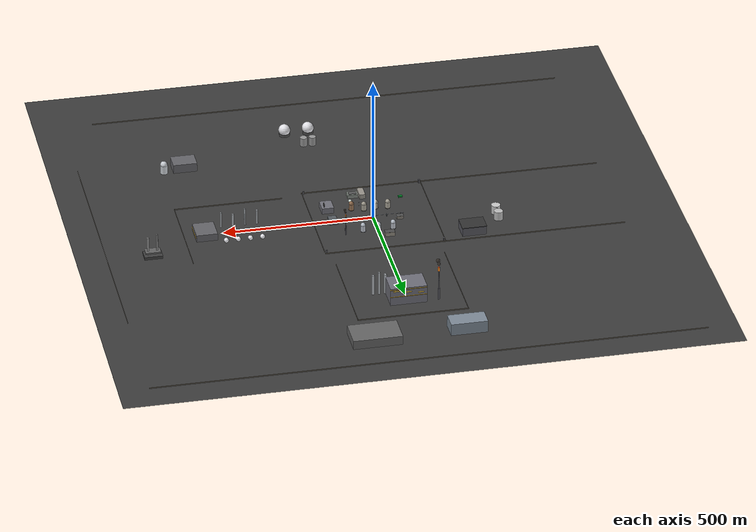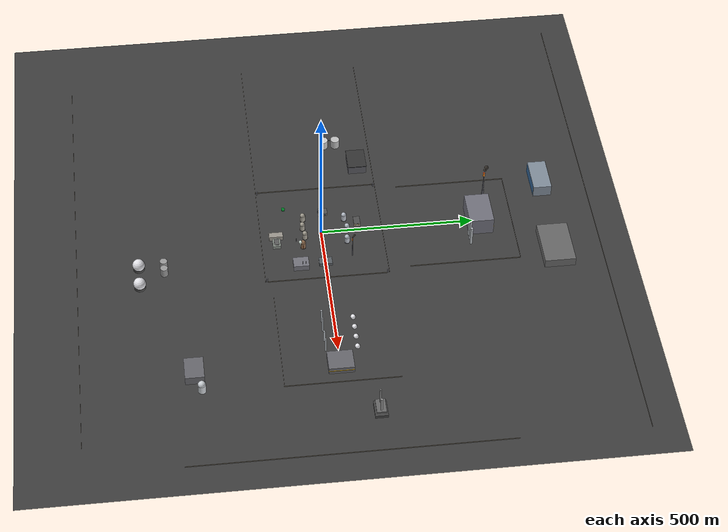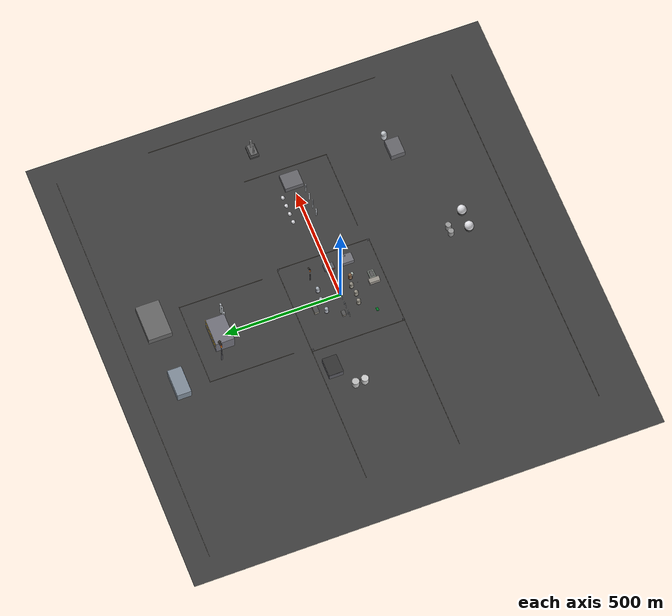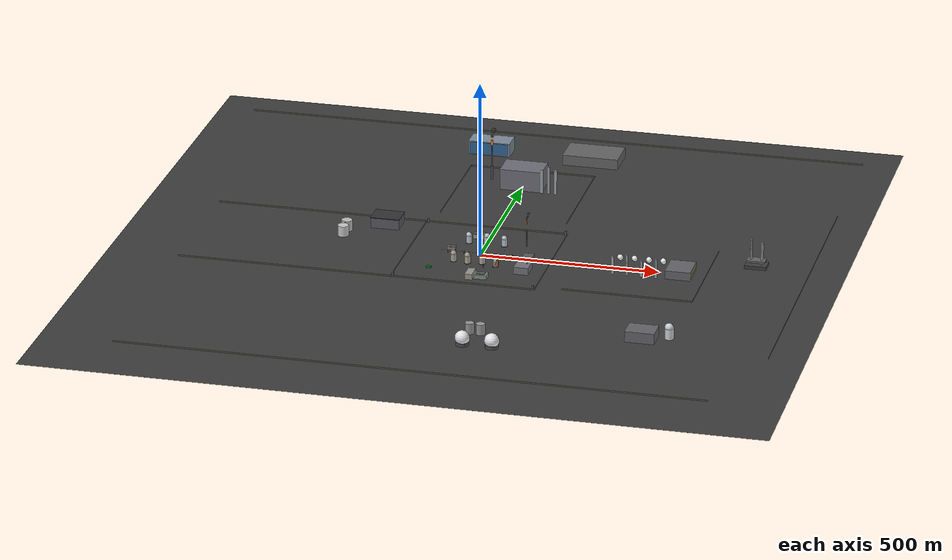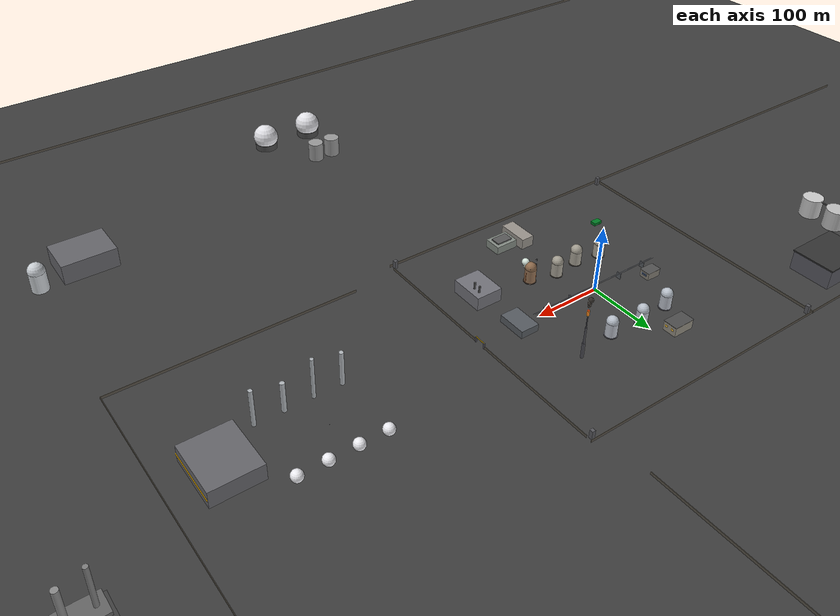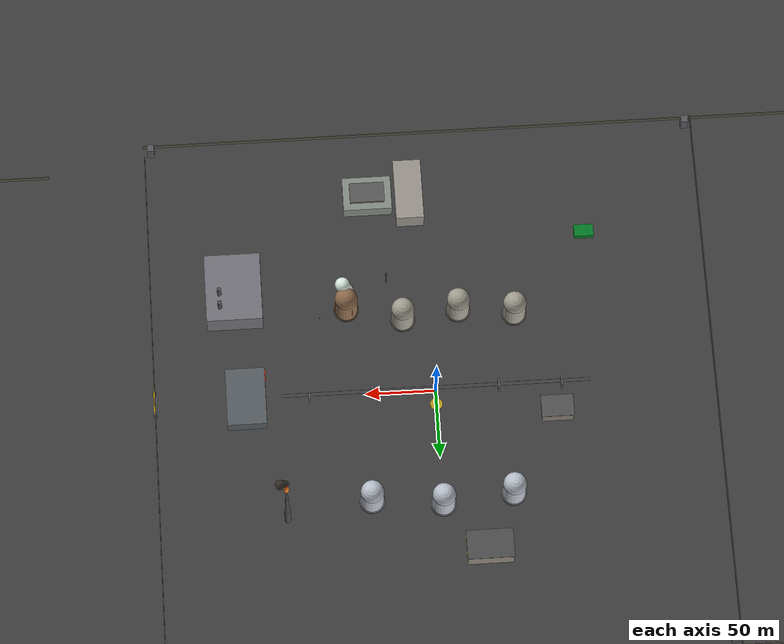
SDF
<sdf version="1.9">
 <world name="lng_terminal">
  <physics name="dart_physics" type="dart">
   <max_step_size>0.002</max_step_size>
   <real_time_factor>1.0</real_time_factor>
  </physics>
  <plugin filename="gz-sim-physics-system" name="gz::sim::systems::Physics"/>
  <plugin filename="gz-sim-scene-broadcaster-system" name="gz::sim::systems::SceneBroadcaster"/>
  <plugin filename="gz-sim-user-commands-system" name="gz::sim::systems::UserCommands"/>
  <plugin filename="gz-sim-sensors-system" name="gz::sim::systems::Sensors"/>
  <plugin filename="gz-sim-particle-emitter-system" name="gz::sim::systems::ParticleEmitter"/>
  <plugin filename="DroneAnimator" name="vesper::DroneAnimator"/>
  <scene>
   <ambient>0.26 0.24 0.22 1.0</ambient>
   <background>0.22 0.26 0.36 1.0</background>
   <shadows>true</shadows>
   <grid>false</grid>
   <origin_visual>false</origin_visual>
   <fog>
    <color>0.28 0.30 0.36 1</color>
    <type>linear</type>
    <start>200</start>
    <end>900</end>
    <density>0.0015</density>
   </fog>
  </scene>
  <light type="directional" name="moonlight">
   <pose>0 0 200 0 0 0</pose>
   <diffuse>0.32 0.34 0.42 1</diffuse>
   <specular>0.10 0.11 0.16 1</specular>
   <direction>0.3 -0.5 -0.8</direction>
   <attenuation>
    <range>3000</range>
    <constant>0.9</constant>
    <linear>0.0</linear>
    <quadratic>0.0</quadratic>
   </attenuation>
  </light>
  <light type="directional" name="dawn_hint">
   <cast_shadows>false</cast_shadows>
   <pose>0 0 100 0 0 0</pose>
   <diffuse>0.20 0.14 0.10 1</diffuse>
   <specular>0.05 0.03 0.02 1</specular>
   <direction>-0.6 -0.4 -0.5</direction>
  </light>
  <light type="point" name="fl_n">
   <cast_shadows>false</cast_shadows>
   <pose>0 150 28 0 0 0</pose>
   <diffuse>0.90 0.70 0.35 1</diffuse>
   <specular>0.18 0.12 0.04 1</specular>
   <attenuation>
    <range>220</range>
    <constant>0.3</constant>
    <linear>0.015</linear>
    <quadratic>0.0001</quadratic>
   </attenuation>
  </light>
  <light type="point" name="fl_s">
   <cast_shadows>false</cast_shadows>
   <pose>0 -150 28 0 0 0</pose>
   <diffuse>0.90 0.70 0.35 1</diffuse>
   <specular>0.18 0.12 0.04 1</specular>
   <attenuation>
    <range>220</range>
    <constant>0.3</constant>
    <linear>0.015</linear>
    <quadratic>0.0001</quadratic>
   </attenuation>
  </light>
  <light type="point" name="fl_e">
   <cast_shadows>false</cast_shadows>
   <pose>150 0 28 0 0 0</pose>
   <diffuse>0.90 0.70 0.35 1</diffuse>
   <specular>0.18 0.12 0.04 1</specular>
   <attenuation>
    <range>220</range>
    <constant>0.3</constant>
    <linear>0.015</linear>
    <quadratic>0.0001</quadratic>
   </attenuation>
  </light>
  <light type="point" name="fl_w">
   <cast_shadows>false</cast_shadows>
   <pose>-150 0 28 0 0 0</pose>
   <diffuse>0.90 0.70 0.35 1</diffuse>
   <specular>0.18 0.12 0.04 1</specular>
   <attenuation>
    <range>220</range>
    <constant>0.3</constant>
    <linear>0.015</linear>
    <quadratic>0.0001</quadratic>
   </attenuation>
  </light>
  <light type="point" name="sector2_glow">
   <cast_shadows>false</cast_shadows>
   <pose>450 0 40 0 0 0</pose>
   <diffuse>0.80 0.55 0.20 1</diffuse>
   <specular>0.1 0.08 0.02 1</specular>
   <attenuation>
    <range>400</range>
    <constant>0.3</constant>
    <linear>0.008</linear>
    <quadratic>0.00003</quadratic>
   </attenuation>
  </light>
  <light type="point" name="sector3_glow">
   <cast_shadows>false</cast_shadows>
   <pose>0 450 60 0 0 0</pose>
   <diffuse>0.78 0.52 0.18 1</diffuse>
   <specular>0.08 0.06 0.02 1</specular>
   <attenuation>
    <range>400</range>
    <constant>0.3</constant>
    <linear>0.008</linear>
    <quadratic>0.00003</quadratic>
   </attenuation>
  </light>
  <light type="point" name="emrg1">
   <cast_shadows>false</cast_shadows>
   <pose>60 -58 5 0 0 0</pose>
   <diffuse>1.0 0.05 0.03 1</diffuse>
   <specular>0.4 0.01 0.01 1</specular>
   <attenuation>
    <range>40</range>
    <constant>0.2</constant>
    <linear>0.07</linear>
    <quadratic>0.03</quadratic>
   </attenuation>
  </light>
  <light type="point" name="emrg2">
   <cast_shadows>false</cast_shadows>
   <pose>40 -65 5 0 0 0</pose>
   <diffuse>1.0 0.05 0.03 1</diffuse>
   <specular>0.3 0.01 0.01 1</specular>
   <attenuation>
    <range>35</range>
    <constant>0.2</constant>
    <linear>0.07</linear>
    <quadratic>0.03</quadratic>
   </attenuation>
  </light>
  <light type="point" name="flare_glow">
   <cast_shadows>false</cast_shadows>
   <pose>110 90 60 0 0 0</pose>
   <diffuse>1.0 0.42 0.06 1</diffuse>
   <specular>0.5 0.18 0.01 1</specular>
   <attenuation>
    <range>160</range>
    <constant>0.25</constant>
    <linear>0.02</linear>
    <quadratic>0.0005</quadratic>
   </attenuation>
  </light>
  <model name="ground">
   <static>true</static>
   <pose>0 0 -0.05 0 0 0</pose>
   <link name="l">
    <collision name="c"><geometry><box><size>2000 2000 0.1</size></box></geometry></collision>
    <visual name="v">
     <geometry><box><size>2000 2000 0.1</size></box></geometry>
     <material>
      <ambient>0.18 0.18 0.18 1</ambient>
      <diffuse>0.24 0.24 0.24 1</diffuse>
      <specular>0.03 0.03 0.03 1</specular>
      <pbr><metal><roughness>0.96</roughness><metalness>0.0</metalness></metal></pbr>
     </material>
    </visual>
   </link>
  </model>
  <model name="cctv_south">
   <static>true</static>
   <pose>30 -85 0 0 0 0</pose>
   <link name="pole_link">
    <collision name="pole_c">
     <pose>0 0 6 0 0 0</pose>
     <geometry><cylinder><radius>0.22</radius><length>12</length></cylinder></geometry>
    </collision>
    <visual name="base_v">
     <pose>0 0 0.4 0 0 0</pose>
     <geometry><cylinder><radius>0.55</radius><length>0.8</length></cylinder></geometry>
     <material>
      <ambient>0.30 0.30 0.30 1</ambient>
      <diffuse>0.38 0.38 0.38 1</diffuse>
      <pbr><metal><roughness>0.85</roughness><metalness>0.1</metalness></metal></pbr>
     </material>
    </visual>
    <visual name="pole_v">
     <pose>0 0 6 0 0 0</pose>
     <geometry><cylinder><radius>0.22</radius><length>12</length></cylinder></geometry>
     <material>
      <ambient>0.22 0.22 0.24 1</ambient>
      <diffuse>0.28 0.28 0.30 1</diffuse>
      <pbr><metal><roughness>0.35</roughness><metalness>0.82</metalness></metal></pbr>
     </material>
    </visual>
    <visual name="arm_v">
     <pose>0 -1.2 11.5 0 1.5707 0</pose>
     <geometry><cylinder><radius>0.11</radius><length>2.4</length></cylinder></geometry>
     <material>
      <ambient>0.22 0.22 0.24 1</ambient>
      <diffuse>0.28 0.28 0.30 1</diffuse>
      <pbr><metal><roughness>0.35</roughness><metalness>0.82</metalness></metal></pbr>
     </material>
    </visual>
    <visual name="cam_housing">
     <pose>0 -2.4 11.5 0 -0.40 1.5707</pose>
     <geometry><box><size>0.55 1.4 0.55</size></box></geometry>
     <material>
      <ambient>0.10 0.10 0.10 1</ambient>
      <diffuse>0.15 0.15 0.15 1</diffuse>
      <specular>0.4 0.4 0.4 1</specular>
      <pbr><metal><roughness>0.40</roughness><metalness>0.5</metalness></metal></pbr>
     </material>
    </visual>
    <visual name="cam_hood">
     <pose>0 -2.4 11.84 0 -0.40 1.5707</pose>
     <geometry><box><size>0.60 1.2 0.10</size></box></geometry>
     <material>
      <ambient>0.06 0.06 0.06 1</ambient>
      <diffuse>0.10 0.10 0.10 1</diffuse>
      <pbr><metal><roughness>0.45</roughness><metalness>0.5</metalness></metal></pbr>
     </material>
    </visual>
    <visual name="cam_lens_ring">
     <pose>-0.72 -2.4 11.5 0 -0.40 0</pose>
     <geometry><cylinder><radius>0.20</radius><length>0.05</length></cylinder></geometry>
     <material>
      <ambient>0.04 0.04 0.04 1</ambient>
      <diffuse>0.06 0.06 0.06 1</diffuse>
      <pbr><metal><roughness>0.3</roughness><metalness>0.7</metalness></metal></pbr>
     </material>
    </visual>
    <visual name="cam_lens_glass">
     <pose>-0.745 -2.4 11.5 0 -0.40 0</pose>
     <geometry><cylinder><radius>0.16</radius><length>0.02</length></cylinder></geometry>
     <material>
      <ambient>0.02 0.06 0.18 1</ambient>
      <diffuse>0.04 0.10 0.28 1</diffuse>
      <specular>0.95 0.95 1.0 1</specular>
      <pbr><metal><roughness>0.05</roughness><metalness>0.4</metalness></metal></pbr>
     </material>
    </visual>
    <visual name="cam_led">
     <pose>-0.60 -2.62 11.72 0 -0.40 0</pose>
     <geometry><sphere><radius>0.028</radius></sphere></geometry>
     <material>
      <ambient>1.0 0.0 0.0 1</ambient>
      <diffuse>1.0 0.0 0.0 1</diffuse>
      <emissive>0.85 0.0 0.0 1</emissive>
     </material>
    </visual>
   </link>
   <link name="cam_sensor_link">
    <pose>0 -2.4 16.0 0 0.18 0.95</pose>
    <inertial><mass>0.001</mass><inertia><ixx>0.0001</ixx><iyy>0.0001</iyy><izz>0.0001</izz></inertia></inertial>
    <sensor name="cctv_south_cam" type="camera">
     <update_rate>5</update_rate>
     <camera>
      <horizontal_fov>1.2217</horizontal_fov>
      <image><width>640</width><height>480</height><format>R8G8B8</format></image>
      <clip><near>0.1</near><far>400</far></clip>
      <noise><type>gaussian</type><mean>0</mean><stddev>0.003</stddev></noise>
      <lens>
       <type>custom</type>
       <custom_function><c1>1.05</c1><c2>-0.1</c2><f>1.0</f><fun>tan</fun></custom_function>
       <scale_to_hfov>true</scale_to_hfov>
      </lens>
     </camera>
    </sensor>
   </link>
   <joint name="cam_south_joint" type="fixed"><parent>pole_link</parent><child>cam_sensor_link</child></joint>
  </model>
  <model name="drone_d1">
   <static>false</static>
   <pose>80 -45 40 0 0 -2.3562</pose>
   <link name="base_link">
    <gravity>false</gravity>
    <inertial>
     <mass>1.0</mass>
     <inertia><ixx>0.05</ixx><iyy>0.05</iyy><izz>0.05</izz><ixy>0</ixy><ixz>0</ixz><iyz>0</iyz></inertia>
    </inertial>
    <visual name="frame">
     <geometry><box><size>0.55 0.55 0.16</size></box></geometry>
     <material>
      <ambient>0.08 0.08 0.10 1</ambient>
      <diffuse>0.13 0.13 0.16 1</diffuse>
      <pbr><metal><roughness>0.24</roughness><metalness>0.82</metalness></metal></pbr>
     </material>
    </visual>
    <visual name="arm_ne">
     <pose>0.27 0.27 0 0 0 0.785</pose>
     <geometry><box><size>0.78 0.07 0.05</size></box></geometry>
     <material><ambient>0.12 0.12 0.14 1</ambient><diffuse>0.18 0.18 0.22 1</diffuse></material>
    </visual>
    <visual name="arm_nw">
     <pose>-0.27 0.27 0 0 0 -0.785</pose>
     <geometry><box><size>0.78 0.07 0.05</size></box></geometry>
     <material><ambient>0.12 0.12 0.14 1</ambient><diffuse>0.18 0.18 0.22 1</diffuse></material>
    </visual>
    <visual name="arm_sw">
     <pose>-0.27 -0.27 0 0 0 0.785</pose>
     <geometry><box><size>0.78 0.07 0.05</size></box></geometry>
     <material><ambient>0.12 0.12 0.14 1</ambient><diffuse>0.18 0.18 0.22 1</diffuse></material>
    </visual>
    <visual name="arm_se">
     <pose>0.27 -0.27 0 0 0 -0.785</pose>
     <geometry><box><size>0.78 0.07 0.05</size></box></geometry>
     <material><ambient>0.12 0.12 0.14 1</ambient><diffuse>0.18 0.18 0.22 1</diffuse></material>
    </visual>
    <visual name="prop_ne">
     <pose>0.47 0.47 0.06 0 0 0</pose>
     <geometry><cylinder><radius>0.22</radius><length>0.005</length></cylinder></geometry>
     <material>
      <ambient>0.40 0.40 0.40 1</ambient>
      <diffuse>0.55 0.55 0.55 1</diffuse>
      <transparency>0.5</transparency>
     </material>
    </visual>
    <visual name="prop_nw">
     <pose>-0.47 0.47 0.06 0 0 0</pose>
     <geometry><cylinder><radius>0.22</radius><length>0.005</length></cylinder></geometry>
     <material>
      <ambient>0.40 0.40 0.40 1</ambient>
      <diffuse>0.55 0.55 0.55 1</diffuse>
      <transparency>0.5</transparency>
     </material>
    </visual>
    <visual name="prop_sw">
     <pose>-0.47 -0.47 0.06 0 0 0</pose>
     <geometry><cylinder><radius>0.22</radius><length>0.005</length></cylinder></geometry>
     <material>
      <ambient>0.40 0.40 0.40 1</ambient>
      <diffuse>0.55 0.55 0.55 1</diffuse>
      <transparency>0.5</transparency>
     </material>
    </visual>
    <visual name="prop_se">
     <pose>0.47 -0.47 0.06 0 0 0</pose>
     <geometry><cylinder><radius>0.22</radius><length>0.005</length></cylinder></geometry>
     <material>
      <ambient>0.40 0.40 0.40 1</ambient>
      <diffuse>0.55 0.55 0.55 1</diffuse>
      <transparency>0.5</transparency>
     </material>
    </visual>
    <visual name="m_ne">
     <pose>0.47 0.47 0.025 0 0 0</pose>
     <geometry><cylinder><radius>0.07</radius><length>0.10</length></cylinder></geometry>
     <material><ambient>0.72 0.66 0.0 1</ambient><diffuse>0.90 0.82 0.0 1</diffuse></material>
    </visual>
    <visual name="m_nw">
     <pose>-0.47 0.47 0.025 0 0 0</pose>
     <geometry><cylinder><radius>0.07</radius><length>0.10</length></cylinder></geometry>
     <material><ambient>0.72 0.66 0.0 1</ambient><diffuse>0.90 0.82 0.0 1</diffuse></material>
    </visual>
    <visual name="m_sw">
     <pose>-0.47 -0.47 0.025 0 0 0</pose>
     <geometry><cylinder><radius>0.07</radius><length>0.10</length></cylinder></geometry>
     <material><ambient>0.72 0.66 0.0 1</ambient><diffuse>0.90 0.82 0.0 1</diffuse></material>
    </visual>
    <visual name="m_se">
     <pose>0.47 -0.47 0.025 0 0 0</pose>
     <geometry><cylinder><radius>0.07</radius><length>0.10</length></cylinder></geometry>
     <material><ambient>0.72 0.66 0.0 1</ambient><diffuse>0.90 0.82 0.0 1</diffuse></material>
    </visual>
    <visual name="gimbal">
     <pose>0 0 -0.12 0 0 0</pose>
     <geometry><sphere><radius>0.075</radius></sphere></geometry>
     <material>
      <ambient>0.05 0.05 0.05 1</ambient>
      <diffuse>0.08 0.08 0.08 1</diffuse>
      <pbr><metal><roughness>0.10</roughness><metalness>0.0</metalness></metal></pbr>
     </material>
    </visual>
    <visual name="nav_red">
     <pose>-0.40 0 0.02 0 0 0</pose>
     <geometry><sphere><radius>0.04</radius></sphere></geometry>
     <material>
      <ambient>0.9 0.0 0.0 1</ambient>
      <diffuse>1.0 0.0 0.0 1</diffuse>
      <emissive>0.85 0.0 0.0 1</emissive>
     </material>
    </visual>
    <visual name="nav_green">
     <pose>0.40 0 0.02 0 0 0</pose>
     <geometry><sphere><radius>0.04</radius></sphere></geometry>
     <material>
      <ambient>0.0 0.9 0.0 1</ambient>
      <diffuse>0.0 1.0 0.0 1</diffuse>
      <emissive>0.0 0.85 0.0 1</emissive>
     </material>
    </visual>
    <visual name="nav_white">
     <pose>0 0 0.10 0 0 0</pose>
     <geometry><sphere><radius>0.035</radius></sphere></geometry>
     <material>
      <ambient>1.0 1.0 1.0 1</ambient>
      <diffuse>1.0 1.0 1.0 1</diffuse>
      <emissive>0.9 0.9 0.9 1</emissive>
     </material>
    </visual>
    <visual name="beacon">
     <pose>0 0 0.18 0 0 0</pose>
     <geometry><sphere><radius>0.07</radius></sphere></geometry>
     <material>
      <ambient>1.0 0.05 0.05 1</ambient>
      <diffuse>1.0 0.10 0.10 1</diffuse>
      <emissive>1.0 0.0 0.0 1</emissive>
     </material>
    </visual>
    <visual name="beacon_glow">
     <pose>0 0 0.18 0 0 0</pose>
     <geometry><sphere><radius>0.14</radius></sphere></geometry>
     <transparency>0.7</transparency>
     <material>
      <ambient>1.0 0.1 0.1 0.3</ambient>
      <diffuse>1.0 0.15 0.15 0.3</diffuse>
      <emissive>0.8 0.0 0.0 1</emissive>
     </material>
    </visual>
    <collision name="c"><geometry><box><size>0.55 0.55 0.16</size></box></geometry></collision>
    <sensor name="drone_cam_main" type="camera">
     <pose>0 0 0.20 0 0.35 3.14159</pose>
     <update_rate>10</update_rate>
     <camera>
      <horizontal_fov>1.0472</horizontal_fov>
      <image><width>640</width><height>480</height><format>R8G8B8</format></image>
      <clip><near>0.5</near><far>400</far></clip>
      <noise><type>gaussian</type><mean>0</mean><stddev>0.002</stddev></noise>
     </camera>
    </sensor>
    <sensor name="drone_cam_back" type="camera">
     <pose>0 0 0.20 0 0.45 0</pose>
     <update_rate>10</update_rate>
     <camera>
      <horizontal_fov>1.0472</horizontal_fov>
      <image><width>640</width><height>480</height><format>R8G8B8</format></image>
      <clip><near>0.5</near><far>400</far></clip>
      <noise><type>gaussian</type><mean>0</mean><stddev>0.002</stddev></noise>
     </camera>
    </sensor>
    <sensor name="drone_cam_wide" type="camera">
     <pose>0 0 0.20 0 0.55 0</pose>
     <update_rate>5</update_rate>
     <camera>
      <horizontal_fov>1.8</horizontal_fov>
      <image><width>640</width><height>480</height><format>R8G8B8</format></image>
      <clip><near>0.5</near><far>400</far></clip>
      <noise><type>gaussian</type><mean>0</mean><stddev>0.002</stddev></noise>
     </camera>
    </sensor>
    <sensor name="drone_cam_track" type="camera">
     <pose>0 0 0.20 0 0.60 0</pose>
     <update_rate>5</update_rate>
     <camera>
      <horizontal_fov>0.5</horizontal_fov>
      <image><width>640</width><height>480</height><format>R8G8B8</format></image>
      <clip><near>0.5</near><far>400</far></clip>
      <noise><type>gaussian</type><mean>0</mean><stddev>0.002</stddev></noise>
     </camera>
    </sensor>
   </link>
  </model>
  <model name="drone_d2">
   <static>false</static>
   <pose>0 10 0.18 0 0 0.4</pose>
   <link name="l">
    <gravity>false</gravity>
    <inertial>
     <mass>0.8</mass>
     <inertia><ixx>0.04</ixx><iyy>0.04</iyy><izz>0.04</izz><ixy>0</ixy><ixz>0</ixz><iyz>0</iyz></inertia>
    </inertial>
    <visual name="frame">
     <geometry><box><size>0.36 0.36 0.10</size></box></geometry>
     <material>
      <ambient>0.10 0.10 0.10 1</ambient>
      <diffuse>0.16 0.16 0.18 1</diffuse>
      <pbr><metal><roughness>0.30</roughness><metalness>0.7</metalness></metal></pbr>
     </material>
    </visual>
    <visual name="arm_a">
     <pose>0.18 0.18 0 0 0 0.785</pose>
     <geometry><box><size>0.55 0.05 0.04</size></box></geometry>
     <material><ambient>0.12 0.12 0.14 1</ambient><diffuse>0.18 0.18 0.22 1</diffuse></material>
    </visual>
    <visual name="arm_b">
     <pose>-0.18 0.18 0 0 0 -0.785</pose>
     <geometry><box><size>0.55 0.05 0.04</size></box></geometry>
     <material><ambient>0.12 0.12 0.14 1</ambient><diffuse>0.18 0.18 0.22 1</diffuse></material>
    </visual>
    <visual name="arm_c">
     <pose>-0.18 -0.18 0 0 0 0.785</pose>
     <geometry><box><size>0.55 0.05 0.04</size></box></geometry>
     <material><ambient>0.12 0.12 0.14 1</ambient><diffuse>0.18 0.18 0.22 1</diffuse></material>
    </visual>
    <visual name="arm_d">
     <pose>0.18 -0.18 0 0 0 -0.785</pose>
     <geometry><box><size>0.55 0.05 0.04</size></box></geometry>
     <material><ambient>0.12 0.12 0.14 1</ambient><diffuse>0.18 0.18 0.22 1</diffuse></material>
    </visual>
    <visual name="m_a">
     <pose>0.32 0.32 0.02 0 0 0</pose>
     <geometry><cylinder><radius>0.045</radius><length>0.07</length></cylinder></geometry>
     <material><ambient>0.55 0.50 0.0 1</ambient><diffuse>0.75 0.68 0.0 1</diffuse></material>
    </visual>
    <visual name="m_b">
     <pose>-0.32 0.32 0.02 0 0 0</pose>
     <geometry><cylinder><radius>0.045</radius><length>0.07</length></cylinder></geometry>
     <material><ambient>0.55 0.50 0.0 1</ambient><diffuse>0.75 0.68 0.0 1</diffuse></material>
    </visual>
    <visual name="m_c">
     <pose>-0.32 -0.32 0.02 0 0 0</pose>
     <geometry><cylinder><radius>0.045</radius><length>0.07</length></cylinder></geometry>
     <material><ambient>0.55 0.50 0.0 1</ambient><diffuse>0.75 0.68 0.0 1</diffuse></material>
    </visual>
    <visual name="m_d">
     <pose>0.32 -0.32 0.02 0 0 0</pose>
     <geometry><cylinder><radius>0.045</radius><length>0.07</length></cylinder></geometry>
     <material><ambient>0.55 0.50 0.0 1</ambient><diffuse>0.75 0.68 0.0 1</diffuse></material>
    </visual>
    <collision name="c"><geometry><box><size>0.36 0.36 0.10</size></box></geometry></collision>
   </link>
  </model>
  <model name="drone_d3">
   <static>false</static>
   <pose>440 30 25 0 0 1.2</pose>
   <link name="l">
    <gravity>false</gravity>
    <inertial>
     <mass>0.9</mass>
     <inertia><ixx>0.045</ixx><iyy>0.045</iyy><izz>0.045</izz><ixy>0</ixy><ixz>0</ixz><iyz>0</iyz></inertia>
    </inertial>
    <visual name="frame">
     <geometry><box><size>0.45 0.45 0.13</size></box></geometry>
     <material>
      <ambient>0.10 0.10 0.10 1</ambient>
      <diffuse>0.16 0.16 0.18 1</diffuse>
      <pbr><metal><roughness>0.28</roughness><metalness>0.75</metalness></metal></pbr>
     </material>
    </visual>
    <visual name="arm_a">
     <pose>0.22 0.22 0 0 0 0.785</pose>
     <geometry><box><size>0.65 0.06 0.04</size></box></geometry>
     <material><ambient>0.12 0.12 0.14 1</ambient><diffuse>0.18 0.18 0.22 1</diffuse></material>
    </visual>
    <visual name="arm_b">
     <pose>-0.22 0.22 0 0 0 -0.785</pose>
     <geometry><box><size>0.65 0.06 0.04</size></box></geometry>
     <material><ambient>0.12 0.12 0.14 1</ambient><diffuse>0.18 0.18 0.22 1</diffuse></material>
    </visual>
    <visual name="arm_c">
     <pose>-0.22 -0.22 0 0 0 0.785</pose>
     <geometry><box><size>0.65 0.06 0.04</size></box></geometry>
     <material><ambient>0.12 0.12 0.14 1</ambient><diffuse>0.18 0.18 0.22 1</diffuse></material>
    </visual>
    <visual name="arm_d">
     <pose>0.22 -0.22 0 0 0 -0.785</pose>
     <geometry><box><size>0.65 0.06 0.04</size></box></geometry>
     <material><ambient>0.12 0.12 0.14 1</ambient><diffuse>0.18 0.18 0.22 1</diffuse></material>
    </visual>
    <visual name="m_a">
     <pose>0.40 0.40 0.025 0 0 0</pose>
     <geometry><cylinder><radius>0.06</radius><length>0.08</length></cylinder></geometry>
     <material><ambient>0.65 0.60 0.0 1</ambient><diffuse>0.85 0.78 0.0 1</diffuse></material>
    </visual>
    <visual name="m_b">
     <pose>-0.40 0.40 0.025 0 0 0</pose>
     <geometry><cylinder><radius>0.06</radius><length>0.08</length></cylinder></geometry>
     <material><ambient>0.65 0.60 0.0 1</ambient><diffuse>0.85 0.78 0.0 1</diffuse></material>
    </visual>
    <visual name="m_c">
     <pose>-0.40 -0.40 0.025 0 0 0</pose>
     <geometry><cylinder><radius>0.06</radius><length>0.08</length></cylinder></geometry>
     <material><ambient>0.65 0.60 0.0 1</ambient><diffuse>0.85 0.78 0.0 1</diffuse></material>
    </visual>
    <visual name="m_d">
     <pose>0.40 -0.40 0.025 0 0 0</pose>
     <geometry><cylinder><radius>0.06</radius><length>0.08</length></cylinder></geometry>
     <material><ambient>0.65 0.60 0.0 1</ambient><diffuse>0.85 0.78 0.0 1</diffuse></material>
    </visual>
    <visual name="nav_r">
     <pose>-0.32 0 0.02 0 0 0</pose>
     <geometry><sphere><radius>0.03</radius></sphere></geometry>
     <material><emissive>0.85 0.0 0.0 1</emissive><diffuse>1.0 0 0 1</diffuse></material>
    </visual>
    <visual name="nav_g">
     <pose>0.32 0 0.02 0 0 0</pose>
     <geometry><sphere><radius>0.03</radius></sphere></geometry>
     <material><emissive>0.0 0.85 0.0 1</emissive><diffuse>0 1 0 1</diffuse></material>
    </visual>
    <collision name="c"><geometry><box><size>0.45 0.45 0.13</size></box></geometry></collision>
   </link>
  </model>
  <model name="drone_pad">
   <static>true</static>
   <pose>0 10 0.02 0 0 0</pose>
   <link name="l">
    <visual name="v">
     <geometry><cylinder><radius>4.5</radius><length>0.04</length></cylinder></geometry>
     <material><ambient>0.58 0.48 0.08 1</ambient><diffuse>0.72 0.60 0.10 1</diffuse></material>
    </visual>
   </link>
  </model>
  <model name="flare_b1">
   <static>true</static>
   <pose>110 90 12 0 0 0</pose>
   <link name="l">
    <collision name="c">
     <geometry><cylinder><radius>2.2</radius><length>24</length></cylinder></geometry>
    </collision>
    <visual name="v">
     <geometry><cylinder><radius>2.2</radius><length>24</length></cylinder></geometry>
     <material>
      <ambient>0.22 0.22 0.25 1</ambient>
      <diffuse>0.30 0.30 0.33 1</diffuse>
      <pbr><metal><roughness>0.35</roughness><metalness>0.86</metalness></metal></pbr>
     </material>
    </visual>
   </link>
  </model>
  <model name="flare_b2">
   <static>true</static>
   <pose>110 90 35 0 0 0</pose>
   <link name="l">
    <collision name="c">
     <geometry><cylinder><radius>1.3</radius><length>26</length></cylinder></geometry>
    </collision>
    <visual name="v">
     <geometry><cylinder><radius>1.3</radius><length>26</length></cylinder></geometry>
     <material>
      <ambient>0.22 0.22 0.25 1</ambient>
      <diffuse>0.30 0.30 0.33 1</diffuse>
      <pbr><metal><roughness>0.35</roughness><metalness>0.86</metalness></metal></pbr>
     </material>
    </visual>
   </link>
  </model>
  <model name="flare_b3">
   <static>true</static>
   <pose>110 90 55 0 0 0</pose>
   <link name="l">
    <collision name="c">
     <geometry><cylinder><radius>0.7</radius><length>22</length></cylinder></geometry>
    </collision>
    <visual name="v">
     <geometry><cylinder><radius>0.7</radius><length>22</length></cylinder></geometry>
     <material>
      <ambient>0.22 0.22 0.25 1</ambient>
      <diffuse>0.30 0.30 0.33 1</diffuse>
      <pbr><metal><roughness>0.35</roughness><metalness>0.86</metalness></metal></pbr>
     </material>
    </visual>
   </link>
  </model>
  <model name="flare_core">
   <static>true</static>
   <pose>110 90 67 0 0 0</pose>
   <link name="l">
    <visual name="v">
     <geometry><cylinder><radius>0.6</radius><length>3</length></cylinder></geometry>
     <material>
      <ambient>1.0 1.0 0.85 1</ambient>
      <diffuse>1.0 1.0 0.92 1</diffuse>
      <emissive>1.0 0.95 0.70 1</emissive>
     </material>
    </visual>
   </link>
  </model>
  <model name="flare_mid">
   <static>true</static>
   <pose>110 90 69 0 0 0</pose>
   <link name="l">
    <visual name="v">
     <geometry><cylinder><radius>1.2</radius><length>5</length></cylinder></geometry>
     <material>
      <ambient>1.0 0.85 0.20 1</ambient>
      <diffuse>1.0 0.90 0.30 1</diffuse>
      <emissive>0.9 0.65 0.10 1</emissive>
     </material>
    </visual>
   </link>
  </model>
  <model name="flare_outer">
   <static>true</static>
   <pose>110 90 71 0 0 0</pose>
   <link name="l">
    <visual name="v">
     <geometry><cylinder><radius>1.8</radius><length>7</length></cylinder></geometry>
     <material>
      <ambient>1.0 0.50 0.08 1</ambient>
      <diffuse>1.0 0.55 0.12 1</diffuse>
      <emissive>0.85 0.32 0.05 1</emissive>
     </material>
    </visual>
   </link>
  </model>
  <model name="flare_tip">
   <static>true</static>
   <pose>110 90 75 0 0 0</pose>
   <link name="l">
    <visual name="v">
     <geometry><sphere><radius>1.4</radius></sphere></geometry>
     <material>
      <ambient>0.85 0.20 0.05 1</ambient>
      <diffuse>0.95 0.25 0.06 1</diffuse>
      <emissive>0.70 0.15 0.03 1</emissive>
     </material>
    </visual>
   </link>
  </model>
  <model name="flare_smk1">
   <static>true</static>
   <pose>110 90 82 0 0 0</pose>
   <link name="l">
    <visual name="v">
     <geometry><sphere><radius>2.2</radius></sphere></geometry>
     <material>
      <ambient>0.18 0.16 0.14 1</ambient>
      <diffuse>0.24 0.22 0.20 1</diffuse>
      <emissive>0.05 0.04 0.03 1</emissive>
     </material>
    </visual>
   </link>
  </model>
  <model name="flare_smk2">
   <static>true</static>
   <pose>112 92 88 0 0 0</pose>
   <link name="l">
    <visual name="v">
     <geometry><sphere><radius>2.8</radius></sphere></geometry>
     <material>
      <ambient>0.16 0.14 0.13 1</ambient>
      <diffuse>0.22 0.20 0.18 1</diffuse>
      <emissive>0.04 0.03 0.02 1</emissive>
     </material>
    </visual>
   </link>
  </model>
  <model name="flare_smk3">
   <static>true</static>
   <pose>114 95 96 0 0 0</pose>
   <link name="l">
    <visual name="v">
     <geometry><sphere><radius>3.5</radius></sphere></geometry>
     <material>
      <ambient>0.14 0.12 0.11 1</ambient>
      <diffuse>0.20 0.18 0.16 1</diffuse>
      <emissive>0.03 0.02 0.02 1</emissive>
     </material>
    </visual>
   </link>
  </model>
  <model name="ref_flare_base">
   <static>true</static>
   <pose>-100 550 20 0 0 0</pose>
   <link name="l">
    <collision name="c">
     <geometry><cylinder><radius>3.5</radius><length>40</length></cylinder></geometry>
    </collision>
    <visual name="v">
     <geometry><cylinder><radius>3.5</radius><length>40</length></cylinder></geometry>
     <material>
      <ambient>0.25 0.25 0.28 1</ambient>
      <diffuse>0.32 0.32 0.35 1</diffuse>
      <pbr><metal><roughness>0.40</roughness><metalness>0.82</metalness></metal></pbr>
     </material>
    </visual>
   </link>
  </model>
  <model name="ref_flare_mid">
   <static>true</static>
   <pose>-100 550 60 0 0 0</pose>
   <link name="l">
    <collision name="c">
     <geometry><cylinder><radius>2.2</radius><length>40</length></cylinder></geometry>
    </collision>
    <visual name="v">
     <geometry><cylinder><radius>2.2</radius><length>40</length></cylinder></geometry>
     <material>
      <ambient>0.25 0.25 0.28 1</ambient>
      <diffuse>0.32 0.32 0.35 1</diffuse>
      <pbr><metal><roughness>0.40</roughness><metalness>0.82</metalness></metal></pbr>
     </material>
    </visual>
   </link>
  </model>
  <model name="ref_flare_top">
   <static>true</static>
   <pose>-100 550 90 0 0 0</pose>
   <link name="l">
    <collision name="c">
     <geometry><cylinder><radius>1.2</radius><length>20</length></cylinder></geometry>
    </collision>
    <visual name="v">
     <geometry><cylinder><radius>1.2</radius><length>20</length></cylinder></geometry>
     <material>
      <ambient>0.25 0.25 0.28 1</ambient>
      <diffuse>0.32 0.32 0.35 1</diffuse>
      <pbr><metal><roughness>0.40</roughness><metalness>0.82</metalness></metal></pbr>
     </material>
    </visual>
   </link>
  </model>
  <model name="ref_flame_core">
   <static>true</static>
   <pose>-100 550 104 0 0 0</pose>
   <link name="l">
    <visual name="v">
     <geometry><cylinder><radius>1.0</radius><length>5</length></cylinder></geometry>
     <material>
      <ambient>1.0 1.0 0.85 1</ambient>
      <diffuse>1.0 1.0 0.92 1</diffuse>
      <emissive>1.0 0.95 0.70 1</emissive>
     </material>
    </visual>
   </link>
  </model>
  <model name="ref_flame_mid">
   <static>true</static>
   <pose>-100 550 107 0 0 0</pose>
   <link name="l">
    <visual name="v">
     <geometry><cylinder><radius>2.2</radius><length>9</length></cylinder></geometry>
     <material>
      <ambient>1.0 0.85 0.20 1</ambient>
      <diffuse>1.0 0.90 0.30 1</diffuse>
      <emissive>0.9 0.65 0.10 1</emissive>
     </material>
    </visual>
   </link>
  </model>
  <model name="ref_flame_outer">
   <static>true</static>
   <pose>-100 550 110 0 0 0</pose>
   <link name="l">
    <visual name="v">
     <geometry><cylinder><radius>3.2</radius><length>13</length></cylinder></geometry>
     <material>
      <ambient>1.0 0.50 0.08 1</ambient>
      <diffuse>1.0 0.55 0.12 1</diffuse>
      <emissive>0.85 0.32 0.05 1</emissive>
     </material>
    </visual>
   </link>
  </model>
  <model name="ref_flame_tip">
   <static>true</static>
   <pose>-100 550 116 0 0 0</pose>
   <link name="l">
    <visual name="v">
     <geometry><sphere><radius>2.8</radius></sphere></geometry>
     <material>
      <ambient>0.85 0.20 0.05 1</ambient>
      <diffuse>0.95 0.25 0.06 1</diffuse>
      <emissive>0.70 0.15 0.03 1</emissive>
     </material>
    </visual>
   </link>
  </model>
  <model name="ref_smk1">
   <static>true</static>
   <pose>-100 552 130 0 0 0</pose>
   <link name="l">
    <visual name="v">
     <geometry><sphere><radius>5</radius></sphere></geometry>
     <material>
      <ambient>0.16 0.14 0.13 1</ambient>
      <diffuse>0.22 0.20 0.18 1</diffuse>
      <emissive>0.04 0.03 0.02 1</emissive>
     </material>
    </visual>
   </link>
  </model>
  <model name="ref_smk2">
   <static>true</static>
   <pose>-96 555 145 0 0 0</pose>
   <link name="l">
    <visual name="v">
     <geometry><sphere><radius>7</radius></sphere></geometry>
     <material>
      <ambient>0.14 0.12 0.11 1</ambient>
      <diffuse>0.20 0.18 0.16 1</diffuse>
      <emissive>0.03 0.02 0.02 1</emissive>
     </material>
    </visual>
   </link>
  </model>
  <model name="s1_fence_n">
   <static>true</static>
   <pose>0 200 2 0 0 0</pose>
   <link name="l">
    <collision name="c"><geometry><box><size>402 0.5 4</size></box></geometry></collision>
    <visual name="v">
     <geometry><box><size>402 0.5 4</size></box></geometry>
     <material>
      <ambient>0.26 0.24 0.22 1</ambient>
      <diffuse>0.34 0.32 0.28 1</diffuse>
      <pbr><metal><roughness>0.95</roughness><metalness>0.0</metalness></metal></pbr>
     </material>
    </visual>
   </link>
  </model>
  <model name="s1_fence_s">
   <static>true</static>
   <pose>0 -200 2 0 0 0</pose>
   <link name="l">
    <collision name="c"><geometry><box><size>402 0.5 4</size></box></geometry></collision>
    <visual name="v">
     <geometry><box><size>402 0.5 4</size></box></geometry>
     <material><ambient>0.26 0.24 0.22 1</ambient><diffuse>0.34 0.32 0.28 1</diffuse></material>
    </visual>
   </link>
  </model>
  <model name="s1_fence_e_n">
   <static>true</static>
   <pose>200 100 2 0 0 1.5707</pose>
   <link name="l">
    <collision name="c"><geometry><box><size>184 0.5 4</size></box></geometry></collision>
    <visual name="v">
     <geometry><box><size>184 0.5 4</size></box></geometry>
     <material><ambient>0.26 0.24 0.22 1</ambient><diffuse>0.34 0.32 0.28 1</diffuse></material>
    </visual>
   </link>
  </model>
  <model name="s1_fence_e_s">
   <static>true</static>
   <pose>200 -100 2 0 0 1.5707</pose>
   <link name="l">
    <collision name="c"><geometry><box><size>184 0.5 4</size></box></geometry></collision>
    <visual name="v">
     <geometry><box><size>184 0.5 4</size></box></geometry>
     <material><ambient>0.26 0.24 0.22 1</ambient><diffuse>0.34 0.32 0.28 1</diffuse></material>
    </visual>
   </link>
  </model>
  <model name="s1_fence_w">
   <static>true</static>
   <pose>-200 0 2 0 0 1.5707</pose>
   <link name="l">
    <collision name="c"><geometry><box><size>402 0.5 4</size></box></geometry></collision>
    <visual name="v">
     <geometry><box><size>402 0.5 4</size></box></geometry>
     <material><ambient>0.26 0.24 0.22 1</ambient><diffuse>0.34 0.32 0.28 1</diffuse></material>
    </visual>
   </link>
  </model>
  <model name="gate_pillar_n">
   <static>true</static>
   <pose>200 8 4 0 0 0</pose>
   <link name="l">
    <visual name="v">
     <geometry><box><size>2 2 8</size></box></geometry>
     <material>
      <ambient>0.25 0.25 0.28 1</ambient>
      <diffuse>0.32 0.32 0.36 1</diffuse>
      <pbr><metal><roughness>0.4</roughness><metalness>0.8</metalness></metal></pbr>
     </material>
    </visual>
    <collision name="c"><geometry><box><size>2 2 8</size></box></geometry></collision>
   </link>
  </model>
  <model name="gate_pillar_s">
   <static>true</static>
   <pose>200 -8 4 0 0 0</pose>
   <link name="l">
    <visual name="v">
     <geometry><box><size>2 2 8</size></box></geometry>
     <material>
      <ambient>0.25 0.25 0.28 1</ambient>
      <diffuse>0.32 0.32 0.36 1</diffuse>
      <pbr><metal><roughness>0.4</roughness><metalness>0.8</metalness></metal></pbr>
     </material>
    </visual>
    <collision name="c"><geometry><box><size>2 2 8</size></box></geometry></collision>
   </link>
  </model>
  <model name="gate_crossbeam">
   <static>true</static>
   <pose>200 0 8 0 0 0</pose>
   <link name="l">
    <visual name="v">
     <geometry><box><size>0.6 18 1.2</size></box></geometry>
     <material>
      <ambient>0.70 0.55 0.0 1</ambient>
      <diffuse>0.90 0.72 0.0 1</diffuse>
      <emissive>0.30 0.20 0.0 1</emissive>
     </material>
    </visual>
   </link>
  </model>
  <model name="tw_ne">
   <static>true</static>
   <pose>195 195 6 0 0 0</pose>
   <link name="l">
    <collision name="c"><geometry><box><size>5 5 12</size></box></geometry></collision>
    <visual name="v">
     <geometry><box><size>5 5 12</size></box></geometry>
     <material>
      <ambient>0.26 0.26 0.28 1</ambient>
      <diffuse>0.34 0.34 0.36 1</diffuse>
      <pbr><metal><roughness>0.55</roughness><metalness>0.45</metalness></metal></pbr>
     </material>
    </visual>
   </link>
  </model>
  <model name="tw_nw">
   <static>true</static>
   <pose>-195 195 6 0 0 0</pose>
   <link name="l">
    <collision name="c"><geometry><box><size>5 5 12</size></box></geometry></collision>
    <visual name="v">
     <geometry><box><size>5 5 12</size></box></geometry>
     <material>
      <ambient>0.26 0.26 0.28 1</ambient>
      <diffuse>0.34 0.34 0.36 1</diffuse>
      <pbr><metal><roughness>0.55</roughness><metalness>0.45</metalness></metal></pbr>
     </material>
    </visual>
   </link>
  </model>
  <model name="tw_se">
   <static>true</static>
   <pose>195 -195 6 0 0 0</pose>
   <link name="l">
    <collision name="c"><geometry><box><size>5 5 12</size></box></geometry></collision>
    <visual name="v">
     <geometry><box><size>5 5 12</size></box></geometry>
     <material>
      <ambient>0.26 0.26 0.28 1</ambient>
      <diffuse>0.34 0.34 0.36 1</diffuse>
      <pbr><metal><roughness>0.55</roughness><metalness>0.45</metalness></metal></pbr>
     </material>
    </visual>
   </link>
  </model>
  <model name="tw_sw">
   <static>true</static>
   <pose>-195 -195 6 0 0 0</pose>
   <link name="l">
    <collision name="c"><geometry><box><size>5 5 12</size></box></geometry></collision>
    <visual name="v">
     <geometry><box><size>5 5 12</size></box></geometry>
     <material>
      <ambient>0.26 0.26 0.28 1</ambient>
      <diffuse>0.34 0.34 0.36 1</diffuse>
      <pbr><metal><roughness>0.55</roughness><metalness>0.45</metalness></metal></pbr>
     </material>
    </visual>
   </link>
  </model>
  <model name="tank_a1">
   <static>true</static>
   <pose>-50 80 0 0 0 0</pose>
   <link name="l">
    <collision name="c">
     <geometry><cylinder><radius>8</radius><length>22</length></cylinder></geometry>
    </collision>
    <visual name="body">
     <pose>0 0 11 0 0 0</pose>
     <geometry><cylinder><radius>8</radius><length>22</length></cylinder></geometry>
     <material>
      <ambient>0.68 0.70 0.74 1</ambient>
      <diffuse>0.76 0.78 0.82 1</diffuse>
      <specular>0.55 0.56 0.60 1</specular>
      <pbr><metal><roughness>0.22</roughness><metalness>0.88</metalness></metal></pbr>
     </material>
    </visual>
    <visual name="dome">
     <pose>0 0 22.5 0 0 0</pose>
     <geometry><sphere><radius>8.2</radius></sphere></geometry>
     <material>
      <ambient>0.65 0.68 0.72 1</ambient>
      <diffuse>0.73 0.76 0.80 1</diffuse>
      <specular>0.60 0.62 0.65 1</specular>
      <pbr><metal><roughness>0.18</roughness><metalness>0.90</metalness></metal></pbr>
     </material>
    </visual>
    <visual name="ring">
     <pose>0 0 0.5 0 0 0</pose>
     <geometry><cylinder><radius>9</radius><length>1.0</length></cylinder></geometry>
     <material>
      <ambient>0.25 0.25 0.28 1</ambient>
      <diffuse>0.32 0.32 0.36 1</diffuse>
      <specular>0.22 0.22 0.24 1</specular>
      <pbr><metal><roughness>0.45</roughness><metalness>0.75</metalness></metal></pbr>
     </material>
    </visual>
   </link>
  </model>
  <model name="tank_a2">
   <static>true</static>
   <pose>0 85 0 0 0 0</pose>
   <link name="l">
    <collision name="c">
     <geometry><cylinder><radius>8</radius><length>22</length></cylinder></geometry>
    </collision>
    <visual name="body">
     <pose>0 0 11 0 0 0</pose>
     <geometry><cylinder><radius>8</radius><length>22</length></cylinder></geometry>
     <material>
      <ambient>0.68 0.70 0.74 1</ambient>
      <diffuse>0.76 0.78 0.82 1</diffuse>
      <specular>0.55 0.56 0.60 1</specular>
      <pbr><metal><roughness>0.22</roughness><metalness>0.88</metalness></metal></pbr>
     </material>
    </visual>
    <visual name="dome">
     <pose>0 0 22.5 0 0 0</pose>
     <geometry><sphere><radius>8.2</radius></sphere></geometry>
     <material>
      <ambient>0.65 0.68 0.72 1</ambient>
      <diffuse>0.73 0.76 0.80 1</diffuse>
      <specular>0.60 0.62 0.65 1</specular>
      <pbr><metal><roughness>0.18</roughness><metalness>0.90</metalness></metal></pbr>
     </material>
    </visual>
    <visual name="ring">
     <pose>0 0 0.5 0 0 0</pose>
     <geometry><cylinder><radius>9</radius><length>1.0</length></cylinder></geometry>
     <material>
      <ambient>0.25 0.25 0.28 1</ambient>
      <diffuse>0.32 0.32 0.36 1</diffuse>
      <specular>0.22 0.22 0.24 1</specular>
      <pbr><metal><roughness>0.45</roughness><metalness>0.75</metalness></metal></pbr>
     </material>
    </visual>
   </link>
  </model>
  <model name="tank_a3">
   <static>true</static>
   <pose>50 80 0 0 0 0</pose>
   <link name="l">
    <collision name="c">
     <geometry><cylinder><radius>8</radius><length>22</length></cylinder></geometry>
    </collision>
    <visual name="body">
     <pose>0 0 11 0 0 0</pose>
     <geometry><cylinder><radius>8</radius><length>22</length></cylinder></geometry>
     <material>
      <ambient>0.68 0.70 0.74 1</ambient>
      <diffuse>0.76 0.78 0.82 1</diffuse>
      <specular>0.55 0.56 0.60 1</specular>
      <pbr><metal><roughness>0.22</roughness><metalness>0.88</metalness></metal></pbr>
     </material>
    </visual>
    <visual name="dome">
     <pose>0 0 22.5 0 0 0</pose>
     <geometry><sphere><radius>8.2</radius></sphere></geometry>
     <material>
      <ambient>0.65 0.68 0.72 1</ambient>
      <diffuse>0.73 0.76 0.80 1</diffuse>
      <specular>0.60 0.62 0.65 1</specular>
      <pbr><metal><roughness>0.18</roughness><metalness>0.90</metalness></metal></pbr>
     </material>
    </visual>
    <visual name="ring">
     <pose>0 0 0.5 0 0 0</pose>
     <geometry><cylinder><radius>9</radius><length>1.0</length></cylinder></geometry>
     <material>
      <ambient>0.25 0.25 0.28 1</ambient>
      <diffuse>0.32 0.32 0.36 1</diffuse>
      <specular>0.22 0.22 0.24 1</specular>
      <pbr><metal><roughness>0.45</roughness><metalness>0.75</metalness></metal></pbr>
     </material>
    </visual>
   </link>
  </model>
  <model name="tank_b1">
   <static>true</static>
   <pose>-60 -55 0 0 0 0</pose>
   <link name="l">
    <collision name="c">
     <geometry><cylinder><radius>8</radius><length>22</length></cylinder></geometry>
    </collision>
    <visual name="body">
     <pose>0 0 11 0 0 0</pose>
     <geometry><cylinder><radius>8</radius><length>22</length></cylinder></geometry>
     <material>
      <ambient>0.60 0.58 0.54 1</ambient>
      <diffuse>0.68 0.66 0.61 1</diffuse>
      <specular>0.28 0.26 0.22 1</specular>
      <pbr><metal><roughness>0.42</roughness><metalness>0.72</metalness></metal></pbr>
     </material>
    </visual>
    <visual name="dome">
     <pose>0 0 22.5 0 0 0</pose>
     <geometry><sphere><radius>8.2</radius></sphere></geometry>
     <material>
      <ambient>0.56 0.54 0.50 1</ambient>
      <diffuse>0.64 0.62 0.57 1</diffuse>
      <specular>0.24 0.22 0.18 1</specular>
      <pbr><metal><roughness>0.48</roughness><metalness>0.68</metalness></metal></pbr>
     </material>
    </visual>
    <visual name="ring">
     <pose>0 0 0.5 0 0 0</pose>
     <geometry><cylinder><radius>9</radius><length>1.0</length></cylinder></geometry>
     <material>
      <ambient>0.20 0.18 0.16 1</ambient>
      <diffuse>0.28 0.26 0.23 1</diffuse>
      <specular>0.08 0.07 0.06 1</specular>
      <pbr><metal><roughness>0.68</roughness><metalness>0.55</metalness></metal></pbr>
     </material>
    </visual>
   </link>
  </model>
  <model name="tank_b2">
   <static>true</static>
   <pose>-20 -60 0 0 0 0</pose>
   <link name="l">
    <collision name="c">
     <geometry><cylinder><radius>8</radius><length>22</length></cylinder></geometry>
    </collision>
    <visual name="body">
     <pose>0 0 11 0 0 0</pose>
     <geometry><cylinder><radius>8</radius><length>22</length></cylinder></geometry>
     <material>
      <ambient>0.60 0.58 0.54 1</ambient>
      <diffuse>0.68 0.66 0.61 1</diffuse>
      <specular>0.28 0.26 0.22 1</specular>
      <pbr><metal><roughness>0.42</roughness><metalness>0.72</metalness></metal></pbr>
     </material>
    </visual>
    <visual name="dome">
     <pose>0 0 22.5 0 0 0</pose>
     <geometry><sphere><radius>8.2</radius></sphere></geometry>
     <material>
      <ambient>0.56 0.54 0.50 1</ambient>
      <diffuse>0.64 0.62 0.57 1</diffuse>
      <specular>0.24 0.22 0.18 1</specular>
      <pbr><metal><roughness>0.48</roughness><metalness>0.68</metalness></metal></pbr>
     </material>
    </visual>
    <visual name="ring">
     <pose>0 0 0.5 0 0 0</pose>
     <geometry><cylinder><radius>9</radius><length>1.0</length></cylinder></geometry>
     <material>
      <ambient>0.20 0.18 0.16 1</ambient>
      <diffuse>0.28 0.26 0.23 1</diffuse>
      <specular>0.08 0.07 0.06 1</specular>
      <pbr><metal><roughness>0.68</roughness><metalness>0.55</metalness></metal></pbr>
     </material>
    </visual>
   </link>
  </model>
  <model name="tank_b3">
   <static>true</static>
   <pose>20 -55 0 0 0 0</pose>
   <link name="l">
    <collision name="c">
     <geometry><cylinder><radius>8</radius><length>22</length></cylinder></geometry>
    </collision>
    <visual name="body">
     <pose>0 0 11 0 0 0</pose>
     <geometry><cylinder><radius>8</radius><length>22</length></cylinder></geometry>
     <material>
      <ambient>0.60 0.58 0.54 1</ambient>
      <diffuse>0.68 0.66 0.61 1</diffuse>
      <specular>0.28 0.26 0.22 1</specular>
      <pbr><metal><roughness>0.42</roughness><metalness>0.72</metalness></metal></pbr>
     </material>
    </visual>
    <visual name="dome">
     <pose>0 0 22.5 0 0 0</pose>
     <geometry><sphere><radius>8.2</radius></sphere></geometry>
     <material>
      <ambient>0.56 0.54 0.50 1</ambient>
      <diffuse>0.64 0.62 0.57 1</diffuse>
      <specular>0.24 0.22 0.18 1</specular>
      <pbr><metal><roughness>0.48</roughness><metalness>0.68</metalness></metal></pbr>
     </material>
    </visual>
    <visual name="ring">
     <pose>0 0 0.5 0 0 0</pose>
     <geometry><cylinder><radius>9</radius><length>1.0</length></cylinder></geometry>
     <material>
      <ambient>0.20 0.18 0.16 1</ambient>
      <diffuse>0.28 0.26 0.23 1</diffuse>
      <specular>0.08 0.07 0.06 1</specular>
      <pbr><metal><roughness>0.68</roughness><metalness>0.55</metalness></metal></pbr>
     </material>
    </visual>
   </link>
  </model>
  <model name="tank_b4">
   <static>true</static>
   <pose>60 -65 0 0 0 0</pose>
   <link name="l">
    <collision name="c">
     <geometry><cylinder><radius>8</radius><length>22</length></cylinder></geometry>
    </collision>
    <visual name="body">
     <pose>0 0 11 0 0 0</pose>
     <geometry><cylinder><radius>8</radius><length>22</length></cylinder></geometry>
     <material>
      <ambient>0.52 0.40 0.30 1</ambient>
      <diffuse>0.60 0.46 0.34 1</diffuse>
      <specular>0.16 0.10 0.06 1</specular>
      <pbr><metal><roughness>0.78</roughness><metalness>0.48</metalness></metal></pbr>
     </material>
    </visual>
    <visual name="dome">
     <pose>0 0 22.5 0 0 0</pose>
     <geometry><sphere><radius>8.2</radius></sphere></geometry>
     <material>
      <ambient>0.48 0.36 0.26 1</ambient>
      <diffuse>0.56 0.42 0.30 1</diffuse>
      <specular>0.10 0.07 0.04 1</specular>
      <pbr><metal><roughness>0.82</roughness><metalness>0.44</metalness></metal></pbr>
     </material>
    </visual>
    <visual name="ring">
     <pose>0 0 0.5 0 0 0</pose>
     <geometry><cylinder><radius>9</radius><length>1.0</length></cylinder></geometry>
     <material>
      <ambient>0.18 0.14 0.10 1</ambient>
      <diffuse>0.24 0.18 0.14 1</diffuse>
      <specular>0.05 0.04 0.03 1</specular>
      <pbr><metal><roughness>0.85</roughness><metalness>0.42</metalness></metal></pbr>
     </material>
    </visual>
    <visual name="rust1">
     <pose>7.95 0 9 0 0 0</pose>
     <geometry><box><size>0.08 1.0 16</size></box></geometry>
     <material>
      <ambient>0.58 0.22 0.04 1</ambient>
      <diffuse>0.66 0.26 0.05 1</diffuse>
      <pbr><metal><roughness>0.95</roughness><metalness>0.10</metalness></metal></pbr>
     </material>
    </visual>
    <visual name="rust2">
     <pose>-4 6.85 12 0 0 0</pose>
     <geometry><box><size>0.08 0.7 12</size></box></geometry>
     <material>
      <ambient>0.55 0.20 0.04 1</ambient>
      <diffuse>0.62 0.23 0.05 1</diffuse>
      <pbr><metal><roughness>0.95</roughness><metalness>0.10</metalness></metal></pbr>
     </material>
    </visual>
    <visual name="flange">
     <pose>8.1 0 4.5 0 1.5707 0</pose>
     <geometry><cylinder><radius>0.4</radius><length>0.7</length></cylinder></geometry>
     <material>
      <ambient>1.0 0.5 0.1 1</ambient>
      <diffuse>1.0 0.6 0.2 1</diffuse>
      <emissive>0.9 0.4 0.0 1</emissive>
      <pbr><metal><roughness>0.2</roughness><metalness>0.8</metalness></metal></pbr>
     </material>
    </visual>
   </link>
  </model>
  <include><uri>model://gas_plume</uri><name>gas_plume_emitter</name><pose>60 -73 4.5 0 0 0</pose></include>
  <include><uri>model://snowfall</uri><name>snowfall_main</name><pose>0 0 80 0 0 0</pose></include>
  <model name="rk1">
   <static>true</static>
   <pose>-90 0 4.5 0 0 0</pose>
   <link name="l">
    <collision name="c"><geometry><box><size>1.2 7 9</size></box></geometry></collision>
    <visual name="v">
     <geometry><box><size>1.2 7 9</size></box></geometry>
     <material>
      <ambient>0.26 0.28 0.30 1</ambient>
      <diffuse>0.34 0.36 0.38 1</diffuse>
      <pbr><metal><roughness>0.38</roughness><metalness>0.82</metalness></metal></pbr>
     </material>
    </visual>
   </link>
  </model>
  <model name="rk2">
   <static>true</static>
   <pose>-45 0 4.5 0 0 0</pose>
   <link name="l">
    <collision name="c"><geometry><box><size>1.2 7 9</size></box></geometry></collision>
    <visual name="v">
     <geometry><box><size>1.2 7 9</size></box></geometry>
     <material>
      <ambient>0.26 0.28 0.30 1</ambient>
      <diffuse>0.34 0.36 0.38 1</diffuse>
      <pbr><metal><roughness>0.38</roughness><metalness>0.82</metalness></metal></pbr>
     </material>
    </visual>
   </link>
  </model>
  <model name="rk3">
   <static>true</static>
   <pose>0 0 4.5 0 0 0</pose>
   <link name="l">
    <collision name="c"><geometry><box><size>1.2 7 9</size></box></geometry></collision>
    <visual name="v">
     <geometry><box><size>1.2 7 9</size></box></geometry>
     <material>
      <ambient>0.26 0.28 0.30 1</ambient>
      <diffuse>0.34 0.36 0.38 1</diffuse>
      <pbr><metal><roughness>0.38</roughness><metalness>0.82</metalness></metal></pbr>
     </material>
    </visual>
   </link>
  </model>
  <model name="rk4">
   <static>true</static>
   <pose>45 0 4.5 0 0 0</pose>
   <link name="l">
    <collision name="c"><geometry><box><size>1.2 7 9</size></box></geometry></collision>
    <visual name="v">
     <geometry><box><size>1.2 7 9</size></box></geometry>
     <material>
      <ambient>0.26 0.28 0.30 1</ambient>
      <diffuse>0.34 0.36 0.38 1</diffuse>
      <pbr><metal><roughness>0.38</roughness><metalness>0.82</metalness></metal></pbr>
     </material>
    </visual>
   </link>
  </model>
  <model name="rk5">
   <static>true</static>
   <pose>90 0 4.5 0 0 0</pose>
   <link name="l">
    <collision name="c"><geometry><box><size>1.2 7 9</size></box></geometry></collision>
    <visual name="v">
     <geometry><box><size>1.2 7 9</size></box></geometry>
     <material>
      <ambient>0.26 0.28 0.30 1</ambient>
      <diffuse>0.34 0.36 0.38 1</diffuse>
      <pbr><metal><roughness>0.38</roughness><metalness>0.82</metalness></metal></pbr>
     </material>
    </visual>
   </link>
  </model>
  <model name="pipe_main">
   <static>true</static>
   <pose>0 1.5 8.5 0 1.5707 0</pose>
   <link name="l">
    <collision name="c">
     <geometry><cylinder><radius>0.28</radius><length>220</length></cylinder></geometry>
    </collision>
    <visual name="v">
     <geometry><cylinder><radius>0.28</radius><length>220</length></cylinder></geometry>
     <material>
      <ambient>0.46 0.48 0.52 1</ambient>
      <diffuse>0.54 0.56 0.60 1</diffuse>
      <pbr><metal><roughness>0.26</roughness><metalness>0.84</metalness></metal></pbr>
     </material>
    </visual>
   </link>
  </model>
  <model name="pipe_sec">
   <static>true</static>
   <pose>0 -1.5 7.2 0 1.5707 0</pose>
   <link name="l">
    <collision name="c">
     <geometry><cylinder><radius>0.18</radius><length>220</length></cylinder></geometry>
    </collision>
    <visual name="v">
     <geometry><cylinder><radius>0.18</radius><length>220</length></cylinder></geometry>
     <material>
      <ambient>0.44 0.46 0.50 1</ambient>
      <diffuse>0.52 0.54 0.58 1</diffuse>
      <pbr><metal><roughness>0.30</roughness><metalness>0.80</metalness></metal></pbr>
     </material>
    </visual>
   </link>
  </model>
  <model name="control_room">
   <static>true</static>
   <pose>-85 20 5.5 0 0 0</pose>
   <link name="l">
    <collision name="c"><geometry><box><size>22 15 11</size></box></geometry></collision>
    <visual name="walls">
     <geometry><box><size>22 15 11</size></box></geometry>
     <material>
      <ambient>0.42 0.40 0.37 1</ambient>
      <diffuse>0.52 0.50 0.46 1</diffuse>
      <pbr><metal><roughness>0.88</roughness><metalness>0.0</metalness></metal></pbr>
     </material>
    </visual>
    <visual name="roof">
     <pose>0 0 5.7 0 0 0</pose>
     <geometry><box><size>23 16 0.4</size></box></geometry>
     <material><ambient>0.25 0.25 0.25 1</ambient><diffuse>0.32 0.32 0.32 1</diffuse></material>
    </visual>
    <visual name="win">
     <pose>11.6 0 1.2 0 0 0</pose>
     <geometry><box><size>0.12 9 3.5</size></box></geometry>
     <material>
      <ambient>0.04 0.08 0.16 1</ambient>
      <diffuse>0.06 0.12 0.22 1</diffuse>
      <emissive>0.05 0.10 0.18 1</emissive>
     </material>
    </visual>
   </link>
  </model>
  <model name="admin_bldg">
   <static>true</static>
   <pose>-30 120 7 0 0 0</pose>
   <link name="l">
    <collision name="c"><geometry><box><size>32 20 14</size></box></geometry></collision>
    <visual name="walls">
     <geometry><box><size>32 20 14</size></box></geometry>
     <material>
      <ambient>0.48 0.46 0.42 1</ambient>
      <diffuse>0.58 0.56 0.51 1</diffuse>
      <pbr><metal><roughness>0.86</roughness><metalness>0.0</metalness></metal></pbr>
     </material>
    </visual>
    <visual name="roof">
     <pose>0 0 7.2 0 0 0</pose>
     <geometry><box><size>33 21 0.5</size></box></geometry>
     <material><ambient>0.24 0.24 0.24 1</ambient><diffuse>0.30 0.30 0.30 1</diffuse></material>
    </visual>
    <visual name="win_a">
     <pose>16.6 -5 1.5 0 0 0</pose>
     <geometry><box><size>0.12 4 3</size></box></geometry>
     <material>
      <ambient>0.8 0.6 0.18 1</ambient>
      <diffuse>1.0 0.78 0.22 1</diffuse>
      <emissive>0.55 0.38 0.08 1</emissive>
     </material>
    </visual>
    <visual name="win_b">
     <pose>16.6 5 1.5 0 0 0</pose>
     <geometry><box><size>0.12 4 3</size></box></geometry>
     <material>
      <ambient>0.8 0.6 0.18 1</ambient>
      <diffuse>1.0 0.78 0.22 1</diffuse>
      <emissive>0.55 0.38 0.08 1</emissive>
     </material>
    </visual>
   </link>
  </model>
  <model name="loading_shed">
   <static>true</static>
   <pose>135 0 5.5 0 0 0</pose>
   <link name="l">
    <collision name="c"><geometry><box><size>28 42 11</size></box></geometry></collision>
    <visual name="v">
     <geometry><box><size>28 42 11</size></box></geometry>
     <material>
      <ambient>0.26 0.28 0.30 1</ambient>
      <diffuse>0.34 0.36 0.38 1</diffuse>
      <pbr><metal><roughness>0.48</roughness><metalness>0.68</metalness></metal></pbr>
     </material>
    </visual>
   </link>
  </model>
  <model name="truck">
   <static>true</static>
   <pose>122 -18 2.2 0 0 1.5707</pose>
   <link name="l">
    <collision name="c"><geometry><box><size>7 3.5 4.5</size></box></geometry></collision>
    <visual name="cab">
     <geometry><box><size>7 3.5 4.5</size></box></geometry>
     <material>
      <ambient>0.68 0.16 0.08 1</ambient>
      <diffuse>0.78 0.20 0.10 1</diffuse>
      <pbr><metal><roughness>0.42</roughness><metalness>0.22</metalness></metal></pbr>
     </material>
    </visual>
    <visual name="trailer">
     <pose>0 -7 -0.6 0 0 0</pose>
     <geometry><box><size>7 13 3.5</size></box></geometry>
     <material>
      <ambient>0.52 0.52 0.52 1</ambient>
      <diffuse>0.62 0.62 0.62 1</diffuse>
      <pbr><metal><roughness>0.58</roughness><metalness>0.52</metalness></metal></pbr>
     </material>
    </visual>
   </link>
  </model>
  <model name="s1_processing_plant">
   <static>true</static>
   <pose>140 -80 10 0 0 0</pose>
   <link name="l">
    <collision name="c"><geometry><box><size>40 50 20</size></box></geometry></collision>
    <visual name="v">
     <geometry><box><size>40 50 20</size></box></geometry>
     <material>
      <ambient>0.35 0.35 0.38 1</ambient>
      <diffuse>0.45 0.45 0.48 1</diffuse>
      <pbr><metal><roughness>0.6</roughness><metalness>0.3</metalness></metal></pbr>
     </material>
    </visual>
    <visual name="chimney1">
     <pose>10 15 15 0 0 0</pose>
     <geometry><cylinder><radius>1.5</radius><length>10</length></cylinder></geometry>
     <material><ambient>0.2 0.2 0.2 1</ambient><diffuse>0.3 0.3 0.3 1</diffuse></material>
    </visual>
    <visual name="chimney2">
     <pose>10 5 15 0 0 0</pose>
     <geometry><cylinder><radius>1.5</radius><length>10</length></cylinder></geometry>
     <material><ambient>0.2 0.2 0.2 1</ambient><diffuse>0.3 0.3 0.3 1</diffuse></material>
    </visual>
   </link>
  </model>
  <model name="s1_compressor_station">
   <static>true</static>
   <pose>40 -150 6 0 0 0</pose>
   <link name="l">
    <collision name="c"><geometry><box><size>35 25 12</size></box></geometry></collision>
    <visual name="v">
     <geometry><box><size>35 25 12</size></box></geometry>
     <material>
      <ambient>0.42 0.45 0.42 1</ambient>
      <diffuse>0.52 0.55 0.52 1</diffuse>
      <pbr><metal><roughness>0.7</roughness><metalness>0.1</metalness></metal></pbr>
     </material>
    </visual>
    <visual name="roof_units">
     <pose>0 0 7 0 0 0</pose>
     <geometry><box><size>25 15 2</size></box></geometry>
     <material><ambient>0.25 0.25 0.25 1</ambient><diffuse>0.35 0.35 0.35 1</diffuse></material>
    </visual>
   </link>
  </model>
  <model name="s1_storage_warehouse">
   <static>true</static>
   <pose>10 -150 8 0 0 0</pose>
   <link name="l">
    <collision name="c"><geometry><box><size>20 45 16</size></box></geometry></collision>
    <visual name="v">
     <geometry><box><size>20 45 16</size></box></geometry>
     <material>
      <ambient>0.5 0.48 0.45 1</ambient>
      <diffuse>0.6 0.58 0.55 1</diffuse>
      <pbr><metal><roughness>0.8</roughness><metalness>0.0</metalness></metal></pbr>
     </material>
    </visual>
   </link>
  </model>
  <model name="muster_shelter">
   <static>true</static>
   <pose>-115 -115 2.2 0 0 0</pose>
   <link name="l">
    <collision name="c"><geometry><box><size>14 9 4.4</size></box></geometry></collision>
    <visual name="v">
     <geometry><box><size>14 9 4.4</size></box></geometry>
     <material>
      <ambient>0.0 0.38 0.10 1</ambient>
      <diffuse>0.0 0.48 0.14 1</diffuse>
      <pbr><metal><roughness>0.80</roughness><metalness>0.0</metalness></metal></pbr>
     </material>
    </visual>
   </link>
  </model>
  <model name="muster_sign">
   <static>true</static>
   <pose>-115 -110 3.8 0 0 0</pose>
   <link name="l">
    <visual name="v">
     <geometry><box><size>0.1 3.5 1.8</size></box></geometry>
     <material>
      <ambient>0.0 0.78 0.18 1</ambient>
      <diffuse>0.0 0.95 0.22 1</diffuse>
      <emissive>0.0 0.52 0.10 1</emissive>
     </material>
    </visual>
   </link>
  </model>
  <model name="gs04_post">
   <static>true</static>
   <pose>52 -52 0 0 0 0</pose>
   <link name="l">
    <visual name="v">
     <pose>0 0 0.9 0 0 0</pose>
     <geometry><cylinder><radius>0.05</radius><length>1.8</length></cylinder></geometry>
     <material>
      <ambient>0.24 0.24 0.26 1</ambient>
      <diffuse>0.30 0.30 0.33 1</diffuse>
      <pbr><metal><roughness>0.32</roughness><metalness>0.82</metalness></metal></pbr>
     </material>
    </visual>
   </link>
  </model>
  <model name="gas_sensor_0">
   <static>true</static>
   <pose>52 -52 1.95 0 0 0</pose>
   <link name="body">
    <visual name="box">
     <geometry><box><size>0.25 0.25 0.4</size></box></geometry>
     <material>
      <ambient>0.82 0.38 0.0 1</ambient>
      <diffuse>0.92 0.46 0.0 1</diffuse>
      <pbr><metal><roughness>0.5</roughness><metalness>0.1</metalness></metal></pbr>
     </material>
    </visual>
    <visual name="led">
     <pose>0 0.135 0.12 0 0 0</pose>
     <geometry><sphere><radius>0.04</radius></sphere></geometry>
     <material>
      <ambient>1.0 0.04 0.04 1</ambient>
      <diffuse>1.0 0.04 0.04 1</diffuse>
      <emissive>0.90 0.0 0.0 1</emissive>
     </material>
    </visual>
    <sensor name="gas_sensor_0" type="gpu_lidar">
     <pose>0 0 0.2 0 0 0</pose>
     <update_rate>10</update_rate>
     <topic>/gas_sensor_0/scan</topic>
     <lidar>
      <scan>
       <horizontal>
        <samples>360</samples>
        <resolution>1</resolution>
        <min_angle>-3.14159</min_angle>
        <max_angle>3.14159</max_angle>
       </horizontal>
       <vertical>
        <samples>1</samples>
        <resolution>1</resolution>
        <min_angle>0</min_angle>
        <max_angle>0</max_angle>
       </vertical>
      </scan>
      <range><min>0.1</min><max>30.0</max><resolution>0.01</resolution></range>
      <noise><type>gaussian</type><mean>0</mean><stddev>0.01</stddev></noise>
     </lidar>
    </sensor>
   </link>
  </model>
  <model name="s2_fence_s">
   <static>true</static>
   <pose>450 -180 2 0 0 0</pose>
   <link name="l">
    <collision name="c"><geometry><box><size>360 0.5 4</size></box></geometry></collision>
    <visual name="v">
     <geometry><box><size>360 0.5 4</size></box></geometry>
     <material><ambient>0.26 0.24 0.22 1</ambient><diffuse>0.34 0.32 0.28 1</diffuse></material>
    </visual>
   </link>
  </model>
  <model name="s2_fence_e">
   <static>true</static>
   <pose>630 0 2 0 0 1.5707</pose>
   <link name="l">
    <collision name="c"><geometry><box><size>362 0.5 4</size></box></geometry></collision>
    <visual name="v">
     <geometry><box><size>362 0.5 4</size></box></geometry>
     <material><ambient>0.26 0.24 0.22 1</ambient><diffuse>0.34 0.32 0.28 1</diffuse></material>
    </visual>
   </link>
  </model>
  <model name="col_1">
   <static>true</static>
   <pose>380 -40 25 0 0 0</pose>
   <link name="l">
    <collision name="c">
     <geometry><cylinder><radius>3</radius><length>50</length></cylinder></geometry>
    </collision>
    <visual name="v">
     <geometry><cylinder><radius>3</radius><length>50</length></cylinder></geometry>
     <material>
      <ambient>0.60 0.62 0.64 1</ambient>
      <diffuse>0.70 0.72 0.74 1</diffuse>
      <pbr><metal><roughness>0.30</roughness><metalness>0.85</metalness></metal></pbr>
     </material>
    </visual>
   </link>
  </model>
  <model name="col_2">
   <static>true</static>
   <pose>420 -40 30 0 0 0</pose>
   <link name="l">
    <collision name="c">
     <geometry><cylinder><radius>2.5</radius><length>60</length></cylinder></geometry>
    </collision>
    <visual name="v">
     <geometry><cylinder><radius>2.5</radius><length>60</length></cylinder></geometry>
     <material>
      <ambient>0.58 0.60 0.62 1</ambient>
      <diffuse>0.68 0.70 0.72 1</diffuse>
      <pbr><metal><roughness>0.30</roughness><metalness>0.85</metalness></metal></pbr>
     </material>
    </visual>
   </link>
  </model>
  <model name="col_3">
   <static>true</static>
   <pose>460 -40 22 0 0 0</pose>
   <link name="l">
    <collision name="c">
     <geometry><cylinder><radius>3.2</radius><length>44</length></cylinder></geometry>
    </collision>
    <visual name="v">
     <geometry><cylinder><radius>3.2</radius><length>44</length></cylinder></geometry>
     <material>
      <ambient>0.60 0.62 0.64 1</ambient>
      <diffuse>0.70 0.72 0.74 1</diffuse>
      <pbr><metal><roughness>0.30</roughness><metalness>0.85</metalness></metal></pbr>
     </material>
    </visual>
   </link>
  </model>
  <model name="col_4">
   <static>true</static>
   <pose>500 -40 27 0 0 0</pose>
   <link name="l">
    <collision name="c">
     <geometry><cylinder><radius>2.8</radius><length>54</length></cylinder></geometry>
    </collision>
    <visual name="v">
     <geometry><cylinder><radius>2.8</radius><length>54</length></cylinder></geometry>
     <material>
      <ambient>0.58 0.60 0.62 1</ambient>
      <diffuse>0.68 0.70 0.72 1</diffuse>
      <pbr><metal><roughness>0.30</roughness><metalness>0.85</metalness></metal></pbr>
     </material>
    </visual>
   </link>
  </model>
  <model name="sph_1">
   <static>true</static>
   <pose>380 60 8 0 0 0</pose>
   <link name="l">
    <collision name="c"><geometry><sphere><radius>8</radius></sphere></geometry></collision>
    <visual name="v">
     <geometry><sphere><radius>8</radius></sphere></geometry>
     <material>
      <ambient>0.88 0.88 0.90 1</ambient>
      <diffuse>0.94 0.94 0.96 1</diffuse>
      <pbr><metal><roughness>0.15</roughness><metalness>0.90</metalness></metal></pbr>
     </material>
    </visual>
    <visual name="legs">
     <pose>0 0 -8 0 0 0</pose>
     <geometry><cylinder><radius>0.3</radius><length>6</length></cylinder></geometry>
     <material><ambient>0.25 0.25 0.28 1</ambient><diffuse>0.32 0.32 0.35 1</diffuse></material>
    </visual>
   </link>
  </model>
  <model name="sph_2">
   <static>true</static>
   <pose>420 60 8 0 0 0</pose>
   <link name="l">
    <collision name="c"><geometry><sphere><radius>8</radius></sphere></geometry></collision>
    <visual name="v">
     <geometry><sphere><radius>8</radius></sphere></geometry>
     <material>
      <ambient>0.88 0.88 0.90 1</ambient>
      <diffuse>0.94 0.94 0.96 1</diffuse>
      <pbr><metal><roughness>0.15</roughness><metalness>0.90</metalness></metal></pbr>
     </material>
    </visual>
   </link>
  </model>
  <model name="sph_3">
   <static>true</static>
   <pose>460 60 8 0 0 0</pose>
   <link name="l">
    <collision name="c"><geometry><sphere><radius>8</radius></sphere></geometry></collision>
    <visual name="v">
     <geometry><sphere><radius>8</radius></sphere></geometry>
     <material>
      <ambient>0.88 0.88 0.90 1</ambient>
      <diffuse>0.94 0.94 0.96 1</diffuse>
      <pbr><metal><roughness>0.15</roughness><metalness>0.90</metalness></metal></pbr>
     </material>
    </visual>
   </link>
  </model>
  <model name="sph_4">
   <static>true</static>
   <pose>500 60 8 0 0 0</pose>
   <link name="l">
    <collision name="c"><geometry><sphere><radius>8</radius></sphere></geometry></collision>
    <visual name="v">
     <geometry><sphere><radius>8</radius></sphere></geometry>
     <material>
      <ambient>0.88 0.88 0.90 1</ambient>
      <diffuse>0.94 0.94 0.96 1</diffuse>
      <pbr><metal><roughness>0.15</roughness><metalness>0.90</metalness></metal></pbr>
     </material>
    </visual>
   </link>
  </model>
  <model name="s2_main">
   <static>true</static>
   <pose>560 0 12 0 0 0</pose>
   <link name="l">
    <collision name="c"><geometry><box><size>70 80 24</size></box></geometry></collision>
    <visual name="v">
     <geometry><box><size>70 80 24</size></box></geometry>
     <material>
      <ambient>0.32 0.32 0.34 1</ambient>
      <diffuse>0.40 0.40 0.42 1</diffuse>
      <pbr><metal><roughness>0.65</roughness><metalness>0.3</metalness></metal></pbr>
     </material>
    </visual>
    <visual name="stripes">
     <pose>35.6 0 0 0 0 0</pose>
     <geometry><box><size>0.6 80 2</size></box></geometry>
     <material>
      <ambient>0.9 0.65 0.0 1</ambient>
      <diffuse>1.0 0.75 0.0 1</diffuse>
      <emissive>0.3 0.22 0.0 1</emissive>
     </material>
    </visual>
   </link>
  </model>
  <model name="s3_fence_e">
   <static>true</static>
   <pose>180 450 2 0 0 0</pose>
   <link name="l">
    <collision name="c"><geometry><box><size>0.5 360 4</size></box></geometry></collision>
    <visual name="v">
     <geometry><box><size>0.5 360 4</size></box></geometry>
     <material><ambient>0.26 0.24 0.22 1</ambient><diffuse>0.34 0.32 0.28 1</diffuse></material>
    </visual>
   </link>
  </model>
  <model name="s3_fence_w">
   <static>true</static>
   <pose>-180 450 2 0 0 0</pose>
   <link name="l">
    <collision name="c"><geometry><box><size>0.5 360 4</size></box></geometry></collision>
    <visual name="v">
     <geometry><box><size>0.5 360 4</size></box></geometry>
     <material><ambient>0.26 0.24 0.22 1</ambient><diffuse>0.34 0.32 0.28 1</diffuse></material>
    </visual>
   </link>
  </model>
  <model name="s3_fence_n">
   <static>true</static>
   <pose>0 630 2 0 0 0</pose>
   <link name="l">
    <collision name="c"><geometry><box><size>362 0.5 4</size></box></geometry></collision>
    <visual name="v">
     <geometry><box><size>362 0.5 4</size></box></geometry>
     <material><ambient>0.26 0.24 0.22 1</ambient><diffuse>0.34 0.32 0.28 1</diffuse></material>
    </visual>
   </link>
  </model>
  <model name="refinery_main">
   <static>true</static>
   <pose>0 520 30 0 0 0</pose>
   <link name="l">
    <collision name="c"><geometry><box><size>120 80 60</size></box></geometry></collision>
    <visual name="v">
     <geometry><box><size>120 80 60</size></box></geometry>
     <material>
      <ambient>0.35 0.35 0.38 1</ambient>
      <diffuse>0.44 0.44 0.48 1</diffuse>
      <specular>0.12 0.12 0.14 1</specular>
      <pbr><metal><roughness>0.55</roughness><metalness>0.45</metalness></metal></pbr>
     </material>
    </visual>
    <visual name="stripe_top">
     <pose>0 40.6 25 0 0 0</pose>
     <geometry><box><size>120 0.6 1.5</size></box></geometry>
     <material>
      <ambient>0.9 0.65 0.0 1</ambient>
      <diffuse>1.0 0.75 0.0 1</diffuse>
      <emissive>0.35 0.25 0.0 1</emissive>
     </material>
    </visual>
    <visual name="stripe_mid">
     <pose>0 40.6 0 0 0 0</pose>
     <geometry><box><size>120 0.6 1.5</size></box></geometry>
     <material>
      <ambient>0.9 0.65 0.0 1</ambient>
      <diffuse>1.0 0.75 0.0 1</diffuse>
      <emissive>0.35 0.25 0.0 1</emissive>
     </material>
    </visual>
    <visual name="wg1">
     <pose>-40 40.7 10 0 0 0</pose>
     <geometry><box><size>20 0.5 4</size></box></geometry>
     <material>
      <ambient>0.7 0.55 0.2 1</ambient>
      <diffuse>0.95 0.78 0.25 1</diffuse>
      <emissive>0.5 0.35 0.08 1</emissive>
     </material>
    </visual>
    <visual name="wg2">
     <pose>0 40.7 15 0 0 0</pose>
     <geometry><box><size>20 0.5 4</size></box></geometry>
     <material>
      <ambient>0.7 0.55 0.2 1</ambient>
      <diffuse>0.95 0.78 0.25 1</diffuse>
      <emissive>0.5 0.35 0.08 1</emissive>
     </material>
    </visual>
    <visual name="wg3">
     <pose>40 40.7 20 0 0 0</pose>
     <geometry><box><size>20 0.5 4</size></box></geometry>
     <material>
      <ambient>0.7 0.55 0.2 1</ambient>
      <diffuse>0.95 0.78 0.25 1</diffuse>
      <emissive>0.5 0.35 0.08 1</emissive>
     </material>
    </visual>
   </link>
  </model>
  <light type="point" name="ref_flare_light">
   <cast_shadows>false</cast_shadows>
   <pose>-100 550 100 0 0 0</pose>
   <diffuse>1.0 0.45 0.08 1</diffuse>
   <specular>0.5 0.2 0.02 1</specular>
   <attenuation>
    <range>300</range>
    <constant>0.2</constant>
    <linear>0.01</linear>
    <quadratic>0.00005</quadratic>
   </attenuation>
  </light>
  <model name="ref_col_1">
   <static>true</static>
   <pose>60 480 35 0 0 0</pose>
   <link name="l">
    <collision name="c">
     <geometry><cylinder><radius>4</radius><length>70</length></cylinder></geometry>
    </collision>
    <visual name="v">
     <geometry><cylinder><radius>4</radius><length>70</length></cylinder></geometry>
     <material>
      <ambient>0.60 0.62 0.64 1</ambient>
      <diffuse>0.70 0.72 0.74 1</diffuse>
      <pbr><metal><roughness>0.3</roughness><metalness>0.85</metalness></metal></pbr>
     </material>
    </visual>
   </link>
  </model>
  <model name="ref_col_2">
   <static>true</static>
   <pose>80 480 40 0 0 0</pose>
   <link name="l">
    <collision name="c">
     <geometry><cylinder><radius>3.5</radius><length>80</length></cylinder></geometry>
    </collision>
    <visual name="v">
     <geometry><cylinder><radius>3.5</radius><length>80</length></cylinder></geometry>
     <material>
      <ambient>0.58 0.60 0.62 1</ambient>
      <diffuse>0.68 0.70 0.72 1</diffuse>
      <pbr><metal><roughness>0.3</roughness><metalness>0.85</metalness></metal></pbr>
     </material>
    </visual>
   </link>
  </model>
  <model name="ref_col_3">
   <static>true</static>
   <pose>100 480 35 0 0 0</pose>
   <link name="l">
    <collision name="c">
     <geometry><cylinder><radius>4</radius><length>70</length></cylinder></geometry>
    </collision>
    <visual name="v">
     <geometry><cylinder><radius>4</radius><length>70</length></cylinder></geometry>
     <material>
      <ambient>0.60 0.62 0.64 1</ambient>
      <diffuse>0.70 0.72 0.74 1</diffuse>
      <pbr><metal><roughness>0.3</roughness><metalness>0.85</metalness></metal></pbr>
     </material>
    </visual>
   </link>
  </model>
  <model name="s4_bldg1">
   <static>true</static>
   <pose>550 -450 15 0 0 0</pose>
   <link name="l">
    <collision name="c"><geometry><box><size>80 60 30</size></box></geometry></collision>
    <visual name="v">
     <geometry><box><size>80 60 30</size></box></geometry>
     <material>
      <ambient>0.32 0.32 0.34 1</ambient>
      <diffuse>0.40 0.40 0.42 1</diffuse>
      <pbr><metal><roughness>0.6</roughness><metalness>0.3</metalness></metal></pbr>
     </material>
    </visual>
   </link>
  </model>
  <model name="s4_tank1">
   <static>true</static>
   <pose>620 -430 15 0 0 0</pose>
   <link name="l">
    <collision name="c">
     <geometry><cylinder><radius>12</radius><length>30</length></cylinder></geometry>
    </collision>
    <visual name="v">
     <geometry><cylinder><radius>12</radius><length>30</length></cylinder></geometry>
     <material>
      <ambient>0.72 0.74 0.76 1</ambient>
      <diffuse>0.82 0.84 0.86 1</diffuse>
      <pbr><metal><roughness>0.2</roughness><metalness>0.9</metalness></metal></pbr>
     </material>
    </visual>
    <visual name="d">
     <pose>0 0 16 0 0 0</pose>
     <geometry><sphere><radius>12.2</radius></sphere></geometry>
     <material>
      <ambient>0.70 0.72 0.74 1</ambient>
      <diffuse>0.80 0.82 0.84 1</diffuse>
      <pbr><metal><roughness>0.18</roughness><metalness>0.92</metalness></metal></pbr>
     </material>
    </visual>
   </link>
  </model>
  <light type="point" name="s4_light">
   <cast_shadows>false</cast_shadows>
   <pose>580 -440 40 0 0 0</pose>
   <diffuse>0.75 0.55 0.22 1</diffuse>
   <specular>0.1 0.08 0.02 1</specular>
   <attenuation>
    <range>400</range>
    <constant>0.3</constant>
    <linear>0.008</linear>
    <quadratic>0.00002</quadratic>
   </attenuation>
  </light>
  <model name="s5_fence_n">
   <static>true</static>
   <pose>-500 200 2 0 0 0</pose>
   <link name="l">
    <collision name="c"><geometry><box><size>600 0.5 4</size></box></geometry></collision>
    <visual name="v">
     <geometry><box><size>600 0.5 4</size></box></geometry>
     <material><ambient>0.26 0.24 0.22 1</ambient><diffuse>0.34 0.32 0.28 1</diffuse></material>
    </visual>
   </link>
  </model>
  <model name="s5_fence_s">
   <static>true</static>
   <pose>-500 -200 2 0 0 0</pose>
   <link name="l">
    <collision name="c"><geometry><box><size>600 0.5 4</size></box></geometry></collision>
    <visual name="v">
     <geometry><box><size>600 0.5 4</size></box></geometry>
     <material><ambient>0.26 0.24 0.22 1</ambient><diffuse>0.34 0.32 0.28 1</diffuse></material>
    </visual>
   </link>
  </model>
  <model name="s5_factory_1">
   <static>true</static>
   <pose>-300 150 15 0 0 0</pose>
   <link name="l">
    <collision name="c"><geometry><box><size>80 60 30</size></box></geometry></collision>
    <visual name="v">
     <geometry><box><size>80 60 30</size></box></geometry>
     <material>
      <ambient>0.3 0.3 0.32 1</ambient>
      <diffuse>0.35 0.35 0.38 1</diffuse>
      <pbr><metal><roughness>0.6</roughness><metalness>0.2</metalness></metal></pbr>
     </material>
    </visual>
    <visual name="roof">
     <pose>0 0 15 0 0 0</pose>
     <geometry><box><size>82 62 2</size></box></geometry>
     <material><ambient>0.2 0.2 0.2 1</ambient></material>
    </visual>
   </link>
  </model>
  <model name="s5_tanks_detailed">
   <static>true</static>
   <pose>-400 50 0 0 0 0</pose>
   <link name="l">
    <collision name="c1">
     <pose>0 0 15 0 0 0</pose>
     <geometry><cylinder><radius>15</radius><length>30</length></cylinder></geometry>
    </collision>
    <visual name="v1">
     <pose>0 0 15 0 0 0</pose>
     <geometry><cylinder><radius>15</radius><length>30</length></cylinder></geometry>
     <material>
      <ambient>0.7 0.7 0.7 1</ambient>
      <diffuse>0.8 0.8 0.8 1</diffuse>
      <pbr><metal><roughness>0.4</roughness><metalness>0.7</metalness></metal></pbr>
     </material>
    </visual>
    <collision name="c2">
     <pose>0 40 15 0 0 0</pose>
     <geometry><cylinder><radius>15</radius><length>30</length></cylinder></geometry>
    </collision>
    <visual name="v2">
     <pose>0 40 15 0 0 0</pose>
     <geometry><cylinder><radius>15</radius><length>30</length></cylinder></geometry>
     <material>
      <ambient>0.65 0.65 0.65 1</ambient>
      <diffuse>0.75 0.75 0.75 1</diffuse>
      <pbr><metal><roughness>0.4</roughness><metalness>0.7</metalness></metal></pbr>
     </material>
    </visual>
    <visual name="pipe">
     <pose>0 20 28 1.5707 0 0</pose>
     <geometry><cylinder><radius>0.8</radius><length>40</length></cylinder></geometry>
     <material><ambient>0.3 0.3 0.3 1</ambient></material>
    </visual>
   </link>
  </model>
  <model name="s6_fence_e">
   <static>true</static>
   <pose>900 0 2 0 0 1.5707</pose>
   <link name="l">
    <visual name="v">
     <geometry><box><size>1000 0.5 4</size></box></geometry>
     <material><ambient>0.26 0.24 0.22 1</ambient><diffuse>0.34 0.32 0.28 1</diffuse></material>
    </visual>
   </link>
  </model>
  <model name="s6_processing">
   <static>true</static>
   <pose>750 100 0 0 0 0</pose>
   <link name="l">
    <collision name="c_base">
     <pose>0 0 5 0 0 0</pose>
     <geometry><box><size>60 40 10</size></box></geometry>
    </collision>
    <visual name="v_base">
     <pose>0 0 5 0 0 0</pose>
     <geometry><box><size>60 40 10</size></box></geometry>
     <material><ambient>0.25 0.25 0.25 1</ambient></material>
    </visual>
    <collision name="c_col1">
     <pose>-15 0 40 0 0 0</pose>
     <geometry><cylinder><radius>3</radius><length>80</length></cylinder></geometry>
    </collision>
    <visual name="v_col1">
     <pose>-15 0 40 0 0 0</pose>
     <geometry><cylinder><radius>3</radius><length>80</length></cylinder></geometry>
     <material>
      <ambient>0.5 0.5 0.5 1</ambient>
      <pbr><metal><roughness>0.5</roughness><metalness>0.6</metalness></metal></pbr>
     </material>
    </visual>
    <collision name="c_col2">
     <pose>15 0 35 0 0 0</pose>
     <geometry><cylinder><radius>4</radius><length>70</length></cylinder></geometry>
    </collision>
    <visual name="v_col2">
     <pose>15 0 35 0 0 0</pose>
     <geometry><cylinder><radius>4</radius><length>70</length></cylinder></geometry>
     <material>
      <ambient>0.55 0.55 0.55 1</ambient>
      <pbr><metal><roughness>0.5</roughness><metalness>0.6</metalness></metal></pbr>
     </material>
    </visual>
    <visual name="v_fins">
     <pose>0 0 20 0 0 0</pose>
     <geometry><box><size>50 30 5</size></box></geometry>
     <material><ambient>0.4 0.4 0.4 1</ambient></material>
    </visual>
   </link>
  </model>
  <model name="s7_fence_n">
   <static>true</static>
   <pose>0 900 2 0 0 0</pose>
   <link name="l">
    <visual name="v">
     <geometry><box><size>1800 0.5 4</size></box></geometry>
     <material><ambient>0.26 0.24 0.22 1</ambient><diffuse>0.34 0.32 0.28 1</diffuse></material>
    </visual>
   </link>
  </model>
  <model name="s7_admin_complex">
   <static>true</static>
   <pose>0 750 0 0 0 0</pose>
   <link name="l">
    <collision name="c_office">
     <pose>-150 0 20 0 0 0</pose>
     <geometry><box><size>120 60 40</size></box></geometry>
    </collision>
    <visual name="v_office">
     <pose>-150 0 20 0 0 0</pose>
     <geometry><box><size>120 60 40</size></box></geometry>
     <material>
      <ambient>0.4 0.45 0.5 1</ambient>
      <diffuse>0.5 0.55 0.6 1</diffuse>
      <pbr><metal><roughness>0.2</roughness><metalness>0.3</metalness></metal></pbr>
     </material>
    </visual>
    <visual name="v_glass">
     <pose>-150 -30.5 20 0 0 0</pose>
     <geometry><box><size>110 0.5 35</size></box></geometry>
     <material>
      <ambient>0.1 0.2 0.3 1</ambient>
      <diffuse>0.2 0.4 0.6 1</diffuse>
      <pbr><metal><roughness>0.1</roughness><metalness>0.9</metalness></metal></pbr>
     </material>
    </visual>
    <collision name="c_warehouse">
     <pose>150 0 15 0 0 0</pose>
     <geometry><box><size>160 100 30</size></box></geometry>
    </collision>
    <visual name="v_warehouse">
     <pose>150 0 15 0 0 0</pose>
     <geometry><box><size>160 100 30</size></box></geometry>
     <material><ambient>0.35 0.35 0.35 1</ambient><diffuse>0.4 0.4 0.4 1</diffuse></material>
    </visual>
   </link>
  </model>
  <model name="s8_fence_s">
   <static>true</static>
   <pose>0 -800 2 0 0 0</pose>
   <link name="l">
    <visual name="v">
     <geometry><box><size>1600 0.5 4</size></box></geometry>
     <material><ambient>0.26 0.24 0.22 1</ambient><diffuse>0.34 0.32 0.28 1</diffuse></material>
    </visual>
   </link>
  </model>
  <model name="s8_storage_farm">
   <static>true</static>
   <pose>100 -600 0 0 0 0</pose>
   <link name="l">
    <collision name="c_sph1">
     <pose>0 0 20 0 0 0</pose>
     <geometry><sphere><radius>20</radius></sphere></geometry>
    </collision>
    <visual name="v_sph1">
     <pose>0 0 20 0 0 0</pose>
     <geometry><sphere><radius>20</radius></sphere></geometry>
     <material>
      <ambient>0.8 0.8 0.82 1</ambient>
      <diffuse>0.9 0.9 0.92 1</diffuse>
      <pbr><metal><roughness>0.2</roughness><metalness>0.8</metalness></metal></pbr>
     </material>
    </visual>
    <visual name="v_base1">
     <pose>0 0 5 0 0 0</pose>
     <geometry><cylinder><radius>18</radius><length>10</length></cylinder></geometry>
     <material><ambient>0.3 0.3 0.3 1</ambient></material>
    </visual>
    <collision name="c_sph2">
     <pose>80 0 20 0 0 0</pose>
     <geometry><sphere><radius>20</radius></sphere></geometry>
    </collision>
    <visual name="v_sph2">
     <pose>80 0 20 0 0 0</pose>
     <geometry><sphere><radius>20</radius></sphere></geometry>
     <material>
      <ambient>0.8 0.8 0.82 1</ambient>
      <diffuse>0.9 0.9 0.92 1</diffuse>
      <pbr><metal><roughness>0.2</roughness><metalness>0.8</metalness></metal></pbr>
     </material>
    </visual>
    <visual name="v_base2">
     <pose>80 0 5 0 0 0</pose>
     <geometry><cylinder><radius>18</radius><length>10</length></cylinder></geometry>
     <material><ambient>0.3 0.3 0.3 1</ambient></material>
    </visual>
    <collision name="c_cyl1">
     <pose>0 80 15 0 0 0</pose>
     <geometry><cylinder><radius>12</radius><length>30</length></cylinder></geometry>
    </collision>
    <visual name="v_cyl1">
     <pose>0 80 15 0 0 0</pose>
     <geometry><cylinder><radius>12</radius><length>30</length></cylinder></geometry>
     <material>
      <ambient>0.6 0.6 0.6 1</ambient>
      <pbr><metal><roughness>0.3</roughness><metalness>0.7</metalness></metal></pbr>
     </material>
    </visual>
    <collision name="c_cyl2">
     <pose>30 80 15 0 0 0</pose>
     <geometry><cylinder><radius>12</radius><length>30</length></cylinder></geometry>
    </collision>
    <visual name="v_cyl2">
     <pose>30 80 15 0 0 0</pose>
     <geometry><cylinder><radius>12</radius><length>30</length></cylinder></geometry>
     <material>
      <ambient>0.6 0.6 0.6 1</ambient>
      <pbr><metal><roughness>0.3</roughness><metalness>0.7</metalness></metal></pbr>
     </material>
    </visual>
   </link>
  </model>
 </world>
</sdf>

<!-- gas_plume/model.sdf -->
<sdf version="1.6">
  <model name="gas_plume">
    <static>true</static>
    <!-- Base link at origin -->
    <link name="plume_link">
      <pose>0 0 0 0 0 0</pose>

      <!-- Puff 0: base emission puff at flange level -->
      <visual name="puff0">
        <pose>0 0 1.5 0 0 0</pose>
        <geometry><sphere><radius>1.2</radius></sphere></geometry>
        <material>
          <ambient>0.82 0.90 0.86 1</ambient>
          <diffuse>0.78 0.88 0.82 1</diffuse>
          <emissive>0.20 0.32 0.24 1</emissive>
        </material>
      </visual>

      <!-- Puff 1: rising, slightly north -->
      <visual name="puff1">
        <pose>-0.4 0.3 4.5 0 0 0</pose>
        <geometry><sphere><radius>1.6</radius></sphere></geometry>
        <material>
          <ambient>0.84 0.91 0.87 1</ambient>
          <diffuse>0.80 0.89 0.84 1</diffuse>
          <emissive>0.18 0.28 0.21 1</emissive>
        </material>
      </visual>

      <!-- Puff 2: larger, slight east lean -->
      <visual name="puff2">
        <pose>0.5 -0.2 8.0 0 0 0</pose>
        <geometry><sphere><radius>2.0</radius></sphere></geometry>
        <material>
          <ambient>0.86 0.92 0.88 1</ambient>
          <diffuse>0.82 0.90 0.86 1</diffuse>
          <emissive>0.15 0.24 0.18 1</emissive>
        </material>
      </visual>

      <!-- Puff 3: billowing outward -->
      <visual name="puff3">
        <pose>-0.6 0.5 11.5 0 0 0</pose>
        <geometry><sphere><radius>2.6</radius></sphere></geometry>
        <material>
          <ambient>0.87 0.92 0.89 1</ambient>
          <diffuse>0.83 0.90 0.86 1</diffuse>
          <emissive>0.12 0.20 0.15 1</emissive>
        </material>
      </visual>

      <!-- Puff 4: large cloud mass above tank top -->
      <visual name="puff4">
        <pose>0.8 -0.6 15.0 0 0 0</pose>
        <geometry><sphere><radius>3.2</radius></sphere></geometry>
        <material>
          <ambient>0.88 0.93 0.90 1</ambient>
          <diffuse>0.84 0.91 0.87 1</diffuse>
          <emissive>0.10 0.16 0.12 1</emissive>
        </material>
      </visual>

      <!-- Puff 5: wide drift cloud, wind-blown north -->
      <visual name="puff5">
        <pose>-1.5 1.2 19.0 0 0 0</pose>
        <geometry><sphere><radius>4.0</radius></sphere></geometry>
        <material>
          <ambient>0.89 0.93 0.90 1</ambient>
          <diffuse>0.85 0.91 0.88 1</diffuse>
          <emissive>0.07 0.12 0.09 1</emissive>
        </material>
      </visual>

      <!-- Puff 6: far drift, very large, faint glow -->
      <visual name="puff6">
        <pose>2.0 -1.0 23.0 0 0 0</pose>
        <geometry><sphere><radius>5.5</radius></sphere></geometry>
        <material>
          <ambient>0.90 0.94 0.91 1</ambient>
          <diffuse>0.86 0.92 0.88 1</diffuse>
          <emissive>0.04 0.08 0.06 1</emissive>
        </material>
      </visual>

      <!-- Small accent: tight puff overlapping puff2 for texture -->
      <visual name="puff_accent1">
        <pose>1.0 0.8 9.5 0 0 0</pose>
        <geometry><sphere><radius>1.3</radius></sphere></geometry>
        <material>
          <ambient>0.85 0.91 0.87 1</ambient>
          <diffuse>0.81 0.89 0.85 1</diffuse>
          <emissive>0.16 0.26 0.19 1</emissive>
        </material>
      </visual>

      <!-- Small accent: overlapping puff4 for lumpy cloud look -->
      <visual name="puff_accent2">
        <pose>-1.2 -1.0 16.5 0 0 0</pose>
        <geometry><sphere><radius>1.8</radius></sphere></geometry>
        <material>
          <ambient>0.87 0.92 0.88 1</ambient>
          <diffuse>0.83 0.90 0.86 1</diffuse>
          <emissive>0.10 0.18 0.13 1</emissive>
        </material>
      </visual>
    </link>
  </model>
</sdf>

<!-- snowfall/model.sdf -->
<sdf version="1.6">
  <model name="snowfall">
    <static>true</static>
    <link name="snow_link">
      <!-- Pitch +90° rotates +X emission to -Z (downward/falling) -->
      <pose>0 0 0 0 1.5707 0</pose>

      <!-- SMALL snowflakes: fast, dense -->
      <particle_emitter name="snow_small" type="box">
        <emitting>true</emitting>
        <size>500 500 0</size>
        <particle_size>0.06 0.06 0.06</particle_size>
        <lifetime>50</lifetime>
        <min_velocity>1.8</min_velocity>
        <max_velocity>3.5</max_velocity>
        <scale_rate>0.01</scale_rate>
        <rate>40</rate>
        <color_start>1.0 1.0 1.0 0.6</color_start>
        <color_end>0.95 0.95 0.98 0.0</color_end>
        <particle_scatter_ratio>0.5</particle_scatter_ratio>
        <material>
          <diffuse>1.0 1.0 1.0</diffuse>
          <specular>1.0 1.0 1.0</specular>
          <pbr>
            <metal>
              <albedo_map>materials/textures/smoke_puff.png</albedo_map>
            </metal>
          </pbr>
        </material>
        <color_range_image>materials/textures/smoke_colors.png</color_range_image>
      </particle_emitter>

      <!-- MEDIUM snowflakes: moderate speed -->
      <particle_emitter name="snow_medium" type="box">
        <emitting>true</emitting>
        <size>500 500 0</size>
        <particle_size>0.15 0.15 0.15</particle_size>
        <lifetime>55</lifetime>
        <min_velocity>1.2</min_velocity>
        <max_velocity>2.8</max_velocity>
        <scale_rate>0.02</scale_rate>
        <rate>25</rate>
        <color_start>1.0 1.0 1.0 0.7</color_start>
        <color_end>0.95 0.95 0.98 0.0</color_end>
        <particle_scatter_ratio>0.7</particle_scatter_ratio>
        <material>
          <diffuse>1.0 1.0 1.0</diffuse>
          <specular>1.0 1.0 1.0</specular>
          <pbr>
            <metal>
              <albedo_map>materials/textures/smoke_puff.png</albedo_map>
            </metal>
          </pbr>
        </material>
        <color_range_image>materials/textures/smoke_colors.png</color_range_image>
      </particle_emitter>

      <!-- LARGE snowflakes: slow, drifty, fewer -->
      <particle_emitter name="snow_large" type="box">
        <emitting>true</emitting>
        <size>500 500 0</size>
        <particle_size>0.28 0.28 0.28</particle_size>
        <lifetime>60</lifetime>
        <min_velocity>0.8</min_velocity>
        <max_velocity>2.0</max_velocity>
        <scale_rate>0.03</scale_rate>
        <rate>10</rate>
        <color_start>1.0 1.0 1.0 0.8</color_start>
        <color_end>0.95 0.95 0.98 0.0</color_end>
        <particle_scatter_ratio>0.9</particle_scatter_ratio>
        <material>
          <diffuse>1.0 1.0 1.0</diffuse>
          <specular>1.0 1.0 1.0</specular>
          <pbr>
            <metal>
              <albedo_map>materials/textures/smoke_puff.png</albedo_map>
            </metal>
          </pbr>
        </material>
        <color_range_image>materials/textures/smoke_colors.png</color_range_image>
      </particle_emitter>
    </link>
  </model>
</sdf>
